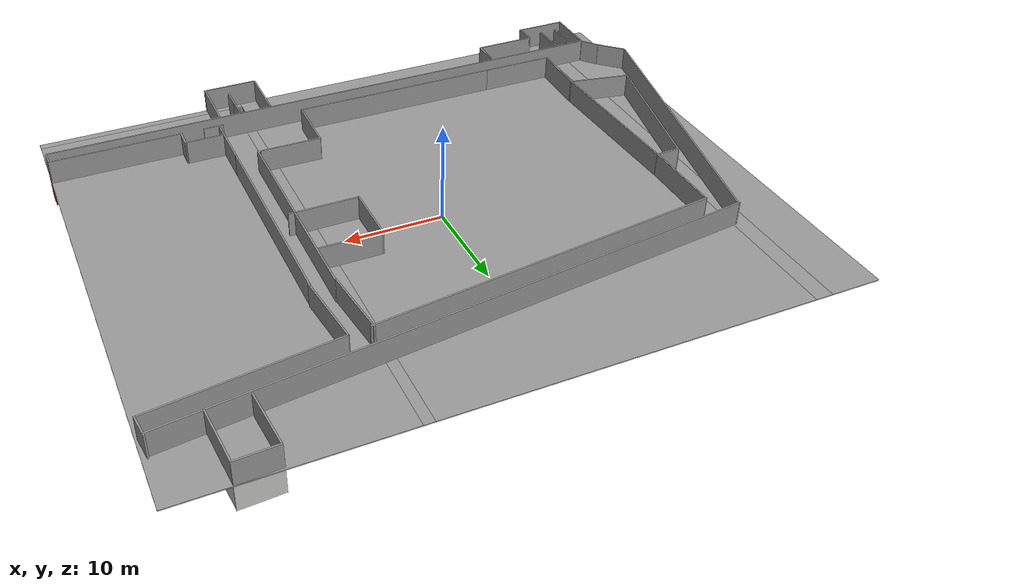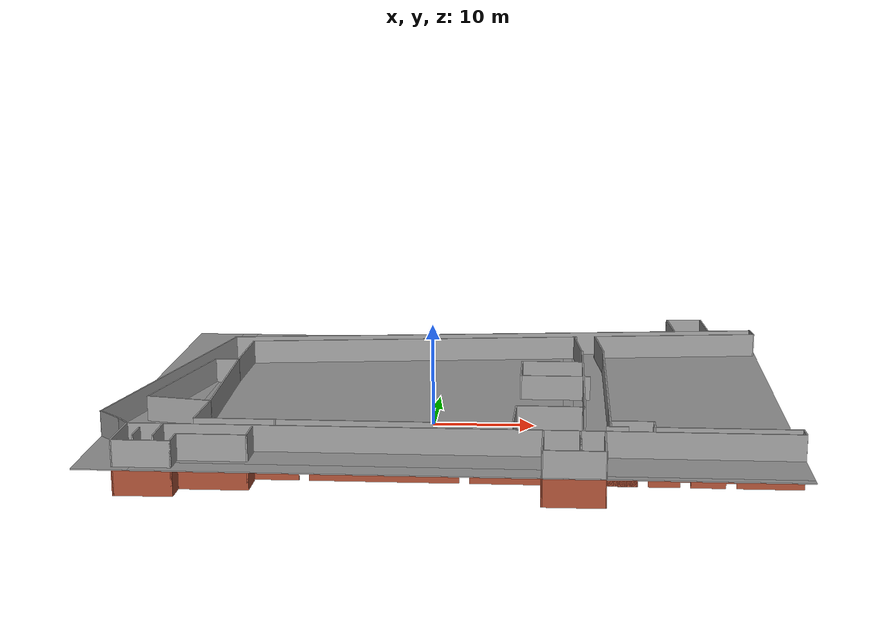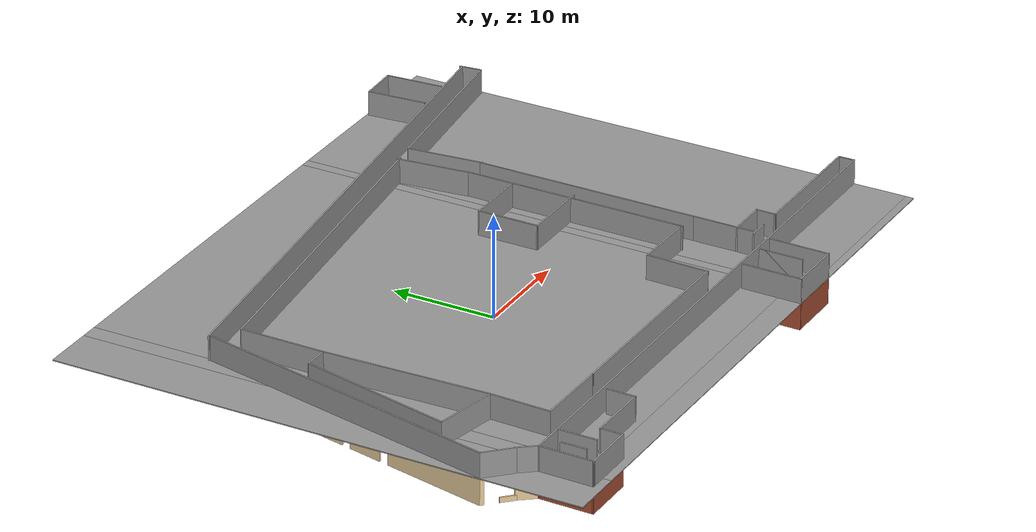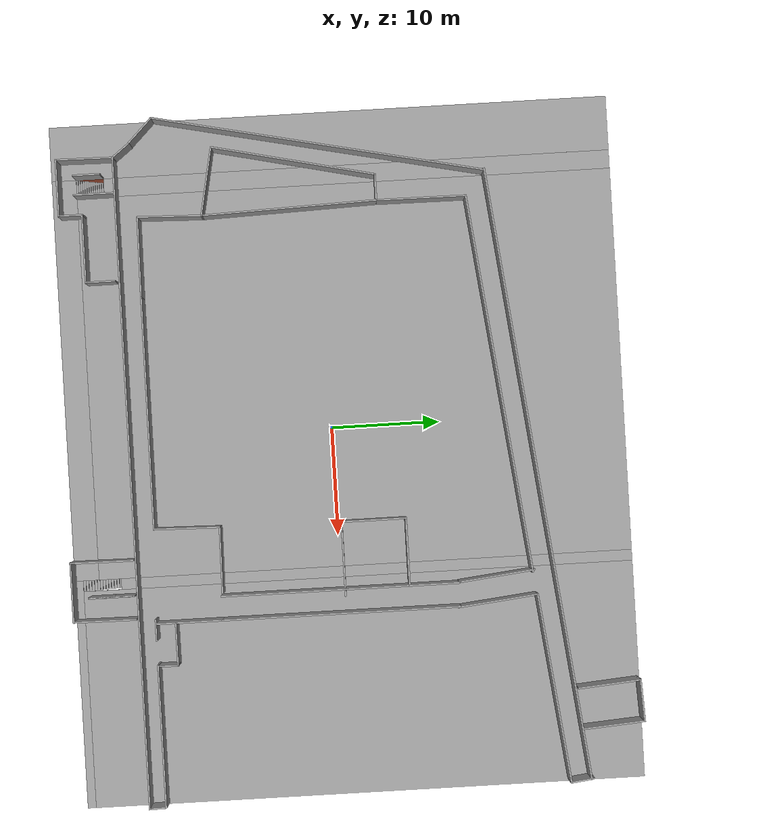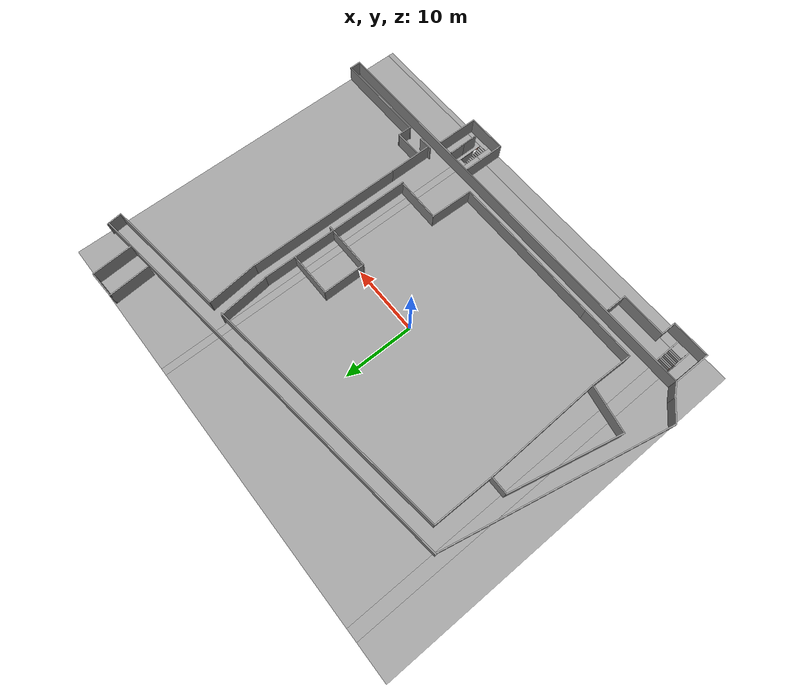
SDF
<?xml version='1.0'?>
<sdf version='1.6'>
  <model name='FokusFloor2-colour'>
    <pose frame=''>2.32223 1.2425 0 0 -0 0</pose>
    <link name='Floor_0'>
      <pose frame=''>1e-06 0 2.5 0 -0 0</pose>
      <visual name='Floor_0_Visual_0'>
        <pose frame=''>-28.8524 0 0.05 0 -0 0</pose>
        <geometry>
          <box>
            <size>4.9433 51.2587 0.1</size>
          </box>
        </geometry>
        <material>
          <script>
            <uri>file://media/materials/scripts/gazebo.material</uri>
            <name>Gazebo/Grey</name>
          </script>
          <ambient>1 1 1 1</ambient>
        </material>
        <meta>
          <layer>1</layer>
        </meta>
      </visual>
      <collision name='Floor_0_Collision_0'>
        <geometry>
          <box>
            <size>4.9433 51.2587 0.1</size>
          </box>
        </geometry>
        <pose frame=''>-28.8524 0 0.05 0 -0 0</pose>
      </collision>
      <visual name='Floor_0_Visual_1'>
        <pose frame=''>-7.97961 -24.5137 0.05 0 -0 0</pose>
        <geometry>
          <box>
            <size>36.8022 2.23126 0.1</size>
          </box>
        </geometry>
        <material>
          <script>
            <uri>file://media/materials/scripts/gazebo.material</uri>
            <name>Gazebo/Grey</name>
          </script>
          <ambient>1 1 1 1</ambient>
        </material>
        <meta>
          <layer>1</layer>
        </meta>
      </visual>
      <collision name='Floor_0_Collision_1'>
        <geometry>
          <box>
            <size>36.8022 2.23126 0.1</size>
          </box>
        </geometry>
        <pose frame=''>-7.97961 -24.5137 0.05 0 -0 0</pose>
      </collision>
      <visual name='Floor_0_Visual_2'>
        <pose frame=''>20.8727 -25.2512 0.05 0 -0 0</pose>
        <geometry>
          <box>
            <size>20.9025 0.756323 0.1</size>
          </box>
        </geometry>
        <material>
          <script>
            <uri>file://media/materials/scripts/gazebo.material</uri>
            <name>Gazebo/Grey</name>
          </script>
          <ambient>1 1 1 1</ambient>
        </material>
        <meta>
          <layer>1</layer>
        </meta>
      </visual>
      <collision name='Floor_0_Collision_2'>
        <geometry>
          <box>
            <size>20.9025 0.756323 0.1</size>
          </box>
        </geometry>
        <pose frame=''>20.8727 -25.2512 0.05 0 -0 0</pose>
      </collision>
      <visual name='Floor_0_Visual_3'>
        <pose frame=''>21.3727 0.378161 0.05 0 -0 0</pose>
        <geometry>
          <box>
            <size>19.9025 50.5024 0.1</size>
          </box>
        </geometry>
        <material>
          <script>
            <uri>file://media/materials/scripts/gazebo.material</uri>
            <name>Gazebo/Grey</name>
          </script>
          <ambient>1 1 1 1</ambient>
        </material>
        <meta>
          <layer>1</layer>
        </meta>
      </visual>
      <collision name='Floor_0_Collision_3'>
        <geometry>
          <box>
            <size>19.9025 50.5024 0.1</size>
          </box>
        </geometry>
        <pose frame=''>21.3727 0.378161 0.05 0 -0 0</pose>
      </collision>
      <visual name='Floor_0_Visual_4'>
        <pose frame=''>-7.1357 1.11563 0.05 0 -0 0</pose>
        <geometry>
          <box>
            <size>35.1144 49.0274 0.1</size>
          </box>
        </geometry>
        <material>
          <script>
            <uri>file://media/materials/scripts/gazebo.material</uri>
            <name>Gazebo/Grey</name>
          </script>
          <ambient>1 1 1 1</ambient>
        </material>
        <meta>
          <layer>1</layer>
        </meta>
      </visual>
      <collision name='Floor_0_Collision_4'>
        <geometry>
          <box>
            <size>35.1144 49.0274 0.1</size>
          </box>
        </geometry>
        <pose frame=''>-7.1357 1.11563 0.05 0 -0 0</pose>
      </collision>
      <visual name='Floor_0_Visual_5'>
        <pose frame=''>10.9215 2.12816 0.05 0 -0 0</pose>
        <geometry>
          <box>
            <size>1 47.0024 0.1</size>
          </box>
        </geometry>
        <material>
          <script>
            <uri>file://media/materials/scripts/gazebo.material</uri>
            <name>Gazebo/Grey</name>
          </script>
          <ambient>1 1 1 1</ambient>
        </material>
        <meta>
          <layer>1</layer>
        </meta>
      </visual>
      <collision name='Floor_0_Collision_5'>
        <geometry>
          <box>
            <size>1 47.0024 0.1</size>
          </box>
        </geometry>
        <pose frame=''>10.9215 2.12816 0.05 0 -0 0</pose>
      </collision>
      <visual name='Floor_0_Visual_6'>
        <pose frame=''>-25.5368 2.3722 0.05 0 -0 0</pose>
        <geometry>
          <box>
            <size>1.68782 46.5143 0.1</size>
          </box>
        </geometry>
        <material>
          <script>
            <uri>file://media/materials/scripts/gazebo.material</uri>
            <name>Gazebo/Grey</name>
          </script>
          <ambient>1 1 1 1</ambient>
        </material>
        <meta>
          <layer>1</layer>
        </meta>
      </visual>
      <collision name='Floor_0_Collision_6'>
        <geometry>
          <box>
            <size>1.68782 46.5143 0.1</size>
          </box>
        </geometry>
        <pose frame=''>-25.5368 2.3722 0.05 0 -0 0</pose>
      </collision>
    </link>
    <link name='Stairs_0'>
      <visual name='Stairs_0_Visual_0'>
        <pose frame=''>10.9215 -21.4897 0.083333 0 -0 0</pose>
        <geometry>
          <box>
            <size>1 0.233333 0.166667</size>
          </box>
        </geometry>
        <material>
          <script>
            <uri>file://media/materials/scripts/gazebo.material</uri>
            <name>Gazebo/Grey</name>
          </script>
          <ambient>1 1 1 1</ambient>
        </material>
        <meta>
          <layer>0</layer>
        </meta>
      </visual>
      <collision name='Stairs_0_Collision_0'>
        <geometry>
          <box>
            <size>1 0.233333 0.166667</size>
          </box>
        </geometry>
        <pose frame=''>10.9215 -21.4897 0.083333 0 -0 0</pose>
      </collision>
      <visual name='Stairs_0_Visual_1'>
        <pose frame=''>10.9215 -21.723 0.25 0 -0 0</pose>
        <geometry>
          <box>
            <size>1 0.233333 0.166667</size>
          </box>
        </geometry>
        <material>
          <script>
            <uri>file://media/materials/scripts/gazebo.material</uri>
            <name>Gazebo/Grey</name>
          </script>
          <ambient>1 1 1 1</ambient>
        </material>
        <meta>
          <layer>0</layer>
        </meta>
      </visual>
      <collision name='Stairs_0_Collision_1'>
        <geometry>
          <box>
            <size>1 0.233333 0.166667</size>
          </box>
        </geometry>
        <pose frame=''>10.9215 -21.723 0.25 0 -0 0</pose>
      </collision>
      <visual name='Stairs_0_Visual_2'>
        <pose frame=''>10.9215 -21.9564 0.416667 0 -0 0</pose>
        <geometry>
          <box>
            <size>1 0.233333 0.166667</size>
          </box>
        </geometry>
        <material>
          <script>
            <uri>file://media/materials/scripts/gazebo.material</uri>
            <name>Gazebo/Grey</name>
          </script>
          <ambient>1 1 1 1</ambient>
        </material>
        <meta>
          <layer>0</layer>
        </meta>
      </visual>
      <collision name='Stairs_0_Collision_2'>
        <geometry>
          <box>
            <size>1 0.233333 0.166667</size>
          </box>
        </geometry>
        <pose frame=''>10.9215 -21.9564 0.416667 0 -0 0</pose>
      </collision>
      <visual name='Stairs_0_Visual_3'>
        <pose frame=''>10.9215 -22.1897 0.583333 0 -0 0</pose>
        <geometry>
          <box>
            <size>1 0.233333 0.166667</size>
          </box>
        </geometry>
        <material>
          <script>
            <uri>file://media/materials/scripts/gazebo.material</uri>
            <name>Gazebo/Grey</name>
          </script>
          <ambient>1 1 1 1</ambient>
        </material>
        <meta>
          <layer>0</layer>
        </meta>
      </visual>
      <collision name='Stairs_0_Collision_3'>
        <geometry>
          <box>
            <size>1 0.233333 0.166667</size>
          </box>
        </geometry>
        <pose frame=''>10.9215 -22.1897 0.583333 0 -0 0</pose>
      </collision>
      <visual name='Stairs_0_Visual_4'>
        <pose frame=''>10.9215 -22.423 0.75 0 -0 0</pose>
        <geometry>
          <box>
            <size>1 0.233333 0.166667</size>
          </box>
        </geometry>
        <material>
          <script>
            <uri>file://media/materials/scripts/gazebo.material</uri>
            <name>Gazebo/Grey</name>
          </script>
          <ambient>1 1 1 1</ambient>
        </material>
        <meta>
          <layer>0</layer>
        </meta>
      </visual>
      <collision name='Stairs_0_Collision_4'>
        <geometry>
          <box>
            <size>1 0.233333 0.166667</size>
          </box>
        </geometry>
        <pose frame=''>10.9215 -22.423 0.75 0 -0 0</pose>
      </collision>
      <visual name='Stairs_0_Visual_5'>
        <pose frame=''>10.9215 -22.6564 0.916667 0 -0 0</pose>
        <geometry>
          <box>
            <size>1 0.233333 0.166667</size>
          </box>
        </geometry>
        <material>
          <script>
            <uri>file://media/materials/scripts/gazebo.material</uri>
            <name>Gazebo/Grey</name>
          </script>
          <ambient>1 1 1 1</ambient>
        </material>
        <meta>
          <layer>0</layer>
        </meta>
      </visual>
      <collision name='Stairs_0_Collision_5'>
        <geometry>
          <box>
            <size>1 0.233333 0.166667</size>
          </box>
        </geometry>
        <pose frame=''>10.9215 -22.6564 0.916667 0 -0 0</pose>
      </collision>
      <visual name='Stairs_0_Visual_6'>
        <pose frame=''>10.9215 -22.8897 1.08333 0 -0 0</pose>
        <geometry>
          <box>
            <size>1 0.233333 0.166667</size>
          </box>
        </geometry>
        <material>
          <script>
            <uri>file://media/materials/scripts/gazebo.material</uri>
            <name>Gazebo/Grey</name>
          </script>
          <ambient>1 1 1 1</ambient>
        </material>
        <meta>
          <layer>0</layer>
        </meta>
      </visual>
      <collision name='Stairs_0_Collision_6'>
        <geometry>
          <box>
            <size>1 0.233333 0.166667</size>
          </box>
        </geometry>
        <pose frame=''>10.9215 -22.8897 1.08333 0 -0 0</pose>
      </collision>
      <visual name='Stairs_0_Visual_7'>
        <pose frame=''>10.9215 -23.123 1.25 0 -0 0</pose>
        <geometry>
          <box>
            <size>1 0.233333 0.166667</size>
          </box>
        </geometry>
        <material>
          <script>
            <uri>file://media/materials/scripts/gazebo.material</uri>
            <name>Gazebo/Grey</name>
          </script>
          <ambient>1 1 1 1</ambient>
        </material>
        <meta>
          <layer>0</layer>
        </meta>
      </visual>
      <collision name='Stairs_0_Collision_7'>
        <geometry>
          <box>
            <size>1 0.233333 0.166667</size>
          </box>
        </geometry>
        <pose frame=''>10.9215 -23.123 1.25 0 -0 0</pose>
      </collision>
      <visual name='Stairs_0_Visual_8'>
        <pose frame=''>10.9215 -23.3564 1.41667 0 -0 0</pose>
        <geometry>
          <box>
            <size>1 0.233333 0.166667</size>
          </box>
        </geometry>
        <material>
          <script>
            <uri>file://media/materials/scripts/gazebo.material</uri>
            <name>Gazebo/Grey</name>
          </script>
          <ambient>1 1 1 1</ambient>
        </material>
        <meta>
          <layer>0</layer>
        </meta>
      </visual>
      <collision name='Stairs_0_Collision_8'>
        <geometry>
          <box>
            <size>1 0.233333 0.166667</size>
          </box>
        </geometry>
        <pose frame=''>10.9215 -23.3564 1.41667 0 -0 0</pose>
      </collision>
      <visual name='Stairs_0_Visual_9'>
        <pose frame=''>10.9215 -23.5897 1.58333 0 -0 0</pose>
        <geometry>
          <box>
            <size>1 0.233333 0.166667</size>
          </box>
        </geometry>
        <material>
          <script>
            <uri>file://media/materials/scripts/gazebo.material</uri>
            <name>Gazebo/Grey</name>
          </script>
          <ambient>1 1 1 1</ambient>
        </material>
        <meta>
          <layer>0</layer>
        </meta>
      </visual>
      <collision name='Stairs_0_Collision_9'>
        <geometry>
          <box>
            <size>1 0.233333 0.166667</size>
          </box>
        </geometry>
        <pose frame=''>10.9215 -23.5897 1.58333 0 -0 0</pose>
      </collision>
      <visual name='Stairs_0_Visual_10'>
        <pose frame=''>10.9215 -23.823 1.75 0 -0 0</pose>
        <geometry>
          <box>
            <size>1 0.233333 0.166667</size>
          </box>
        </geometry>
        <material>
          <script>
            <uri>file://media/materials/scripts/gazebo.material</uri>
            <name>Gazebo/Grey</name>
          </script>
          <ambient>1 1 1 1</ambient>
        </material>
        <meta>
          <layer>0</layer>
        </meta>
      </visual>
      <collision name='Stairs_0_Collision_10'>
        <geometry>
          <box>
            <size>1 0.233333 0.166667</size>
          </box>
        </geometry>
        <pose frame=''>10.9215 -23.823 1.75 0 -0 0</pose>
      </collision>
      <visual name='Stairs_0_Visual_11'>
        <pose frame=''>10.9215 -24.0564 1.91667 0 -0 0</pose>
        <geometry>
          <box>
            <size>1 0.233333 0.166667</size>
          </box>
        </geometry>
        <material>
          <script>
            <uri>file://media/materials/scripts/gazebo.material</uri>
            <name>Gazebo/Grey</name>
          </script>
          <ambient>1 1 1 1</ambient>
        </material>
        <meta>
          <layer>0</layer>
        </meta>
      </visual>
      <collision name='Stairs_0_Collision_11'>
        <geometry>
          <box>
            <size>1 0.233333 0.166667</size>
          </box>
        </geometry>
        <pose frame=''>10.9215 -24.0564 1.91667 0 -0 0</pose>
      </collision>
      <visual name='Stairs_0_Visual_12'>
        <pose frame=''>10.9215 -24.2897 2.08333 0 -0 0</pose>
        <geometry>
          <box>
            <size>1 0.233333 0.166667</size>
          </box>
        </geometry>
        <material>
          <script>
            <uri>file://media/materials/scripts/gazebo.material</uri>
            <name>Gazebo/Grey</name>
          </script>
          <ambient>1 1 1 1</ambient>
        </material>
        <meta>
          <layer>0</layer>
        </meta>
      </visual>
      <collision name='Stairs_0_Collision_12'>
        <geometry>
          <box>
            <size>1 0.233333 0.166667</size>
          </box>
        </geometry>
        <pose frame=''>10.9215 -24.2897 2.08333 0 -0 0</pose>
      </collision>
      <visual name='Stairs_0_Visual_13'>
        <pose frame=''>10.9215 -24.523 2.25 0 -0 0</pose>
        <geometry>
          <box>
            <size>1 0.233333 0.166667</size>
          </box>
        </geometry>
        <material>
          <script>
            <uri>file://media/materials/scripts/gazebo.material</uri>
            <name>Gazebo/Grey</name>
          </script>
          <ambient>1 1 1 1</ambient>
        </material>
        <meta>
          <layer>0</layer>
        </meta>
      </visual>
      <collision name='Stairs_0_Collision_13'>
        <geometry>
          <box>
            <size>1 0.233333 0.166667</size>
          </box>
        </geometry>
        <pose frame=''>10.9215 -24.523 2.25 0 -0 0</pose>
      </collision>
      <visual name='Stairs_0_Visual_14'>
        <pose frame=''>10.9215 -24.7564 2.41667 0 -0 0</pose>
        <geometry>
          <box>
            <size>1 0.233333 0.166667</size>
          </box>
        </geometry>
        <material>
          <script>
            <uri>file://media/materials/scripts/gazebo.material</uri>
            <name>Gazebo/Grey</name>
          </script>
          <ambient>1 1 1 1</ambient>
        </material>
        <meta>
          <layer>0</layer>
        </meta>
      </visual>
      <collision name='Stairs_0_Collision_14'>
        <geometry>
          <box>
            <size>1 0.233333 0.166667</size>
          </box>
        </geometry>
        <pose frame=''>10.9215 -24.7564 2.41667 0 -0 0</pose>
      </collision>
    </link>
    <link name='Stairs_1'>
      <visual name='Stairs_1_Visual_0'>
        <pose frame=''>-25.5368 -20.9687 0.083333 0 -0 0</pose>
        <geometry>
          <box>
            <size>1.68782 0.167542 0.166667</size>
          </box>
        </geometry>
        <material>
          <script>
            <uri>file://media/materials/scripts/gazebo.material</uri>
            <name>Gazebo/Grey</name>
          </script>
          <ambient>1 1 1 1</ambient>
        </material>
        <meta>
          <layer>0</layer>
        </meta>
      </visual>
      <collision name='Stairs_1_Collision_0'>
        <geometry>
          <box>
            <size>1.68782 0.167542 0.166667</size>
          </box>
        </geometry>
        <pose frame=''>-25.5368 -20.9687 0.083333 0 -0 0</pose>
      </collision>
      <visual name='Stairs_1_Visual_1'>
        <pose frame=''>-25.5368 -21.1363 0.25 0 -0 0</pose>
        <geometry>
          <box>
            <size>1.68782 0.167542 0.166667</size>
          </box>
        </geometry>
        <material>
          <script>
            <uri>file://media/materials/scripts/gazebo.material</uri>
            <name>Gazebo/Grey</name>
          </script>
          <ambient>1 1 1 1</ambient>
        </material>
        <meta>
          <layer>0</layer>
        </meta>
      </visual>
      <collision name='Stairs_1_Collision_1'>
        <geometry>
          <box>
            <size>1.68782 0.167542 0.166667</size>
          </box>
        </geometry>
        <pose frame=''>-25.5368 -21.1363 0.25 0 -0 0</pose>
      </collision>
      <visual name='Stairs_1_Visual_2'>
        <pose frame=''>-25.5368 -21.3038 0.416667 0 -0 0</pose>
        <geometry>
          <box>
            <size>1.68782 0.167542 0.166667</size>
          </box>
        </geometry>
        <material>
          <script>
            <uri>file://media/materials/scripts/gazebo.material</uri>
            <name>Gazebo/Grey</name>
          </script>
          <ambient>1 1 1 1</ambient>
        </material>
        <meta>
          <layer>0</layer>
        </meta>
      </visual>
      <collision name='Stairs_1_Collision_2'>
        <geometry>
          <box>
            <size>1.68782 0.167542 0.166667</size>
          </box>
        </geometry>
        <pose frame=''>-25.5368 -21.3038 0.416667 0 -0 0</pose>
      </collision>
      <visual name='Stairs_1_Visual_3'>
        <pose frame=''>-25.5368 -21.4714 0.583333 0 -0 0</pose>
        <geometry>
          <box>
            <size>1.68782 0.167542 0.166667</size>
          </box>
        </geometry>
        <material>
          <script>
            <uri>file://media/materials/scripts/gazebo.material</uri>
            <name>Gazebo/Grey</name>
          </script>
          <ambient>1 1 1 1</ambient>
        </material>
        <meta>
          <layer>0</layer>
        </meta>
      </visual>
      <collision name='Stairs_1_Collision_3'>
        <geometry>
          <box>
            <size>1.68782 0.167542 0.166667</size>
          </box>
        </geometry>
        <pose frame=''>-25.5368 -21.4714 0.583333 0 -0 0</pose>
      </collision>
      <visual name='Stairs_1_Visual_4'>
        <pose frame=''>-25.5368 -21.6389 0.75 0 -0 0</pose>
        <geometry>
          <box>
            <size>1.68782 0.167542 0.166667</size>
          </box>
        </geometry>
        <material>
          <script>
            <uri>file://media/materials/scripts/gazebo.material</uri>
            <name>Gazebo/Grey</name>
          </script>
          <ambient>1 1 1 1</ambient>
        </material>
        <meta>
          <layer>0</layer>
        </meta>
      </visual>
      <collision name='Stairs_1_Collision_4'>
        <geometry>
          <box>
            <size>1.68782 0.167542 0.166667</size>
          </box>
        </geometry>
        <pose frame=''>-25.5368 -21.6389 0.75 0 -0 0</pose>
      </collision>
      <visual name='Stairs_1_Visual_5'>
        <pose frame=''>-25.5368 -21.8064 0.916667 0 -0 0</pose>
        <geometry>
          <box>
            <size>1.68782 0.167542 0.166667</size>
          </box>
        </geometry>
        <material>
          <script>
            <uri>file://media/materials/scripts/gazebo.material</uri>
            <name>Gazebo/Grey</name>
          </script>
          <ambient>1 1 1 1</ambient>
        </material>
        <meta>
          <layer>0</layer>
        </meta>
      </visual>
      <collision name='Stairs_1_Collision_5'>
        <geometry>
          <box>
            <size>1.68782 0.167542 0.166667</size>
          </box>
        </geometry>
        <pose frame=''>-25.5368 -21.8064 0.916667 0 -0 0</pose>
      </collision>
      <visual name='Stairs_1_Visual_6'>
        <pose frame=''>-25.5368 -21.974 1.08333 0 -0 0</pose>
        <geometry>
          <box>
            <size>1.68782 0.167542 0.166667</size>
          </box>
        </geometry>
        <material>
          <script>
            <uri>file://media/materials/scripts/gazebo.material</uri>
            <name>Gazebo/Grey</name>
          </script>
          <ambient>1 1 1 1</ambient>
        </material>
        <meta>
          <layer>0</layer>
        </meta>
      </visual>
      <collision name='Stairs_1_Collision_6'>
        <geometry>
          <box>
            <size>1.68782 0.167542 0.166667</size>
          </box>
        </geometry>
        <pose frame=''>-25.5368 -21.974 1.08333 0 -0 0</pose>
      </collision>
      <visual name='Stairs_1_Visual_7'>
        <pose frame=''>-25.5368 -22.1415 1.25 0 -0 0</pose>
        <geometry>
          <box>
            <size>1.68782 0.167542 0.166667</size>
          </box>
        </geometry>
        <material>
          <script>
            <uri>file://media/materials/scripts/gazebo.material</uri>
            <name>Gazebo/Grey</name>
          </script>
          <ambient>1 1 1 1</ambient>
        </material>
        <meta>
          <layer>0</layer>
        </meta>
      </visual>
      <collision name='Stairs_1_Collision_7'>
        <geometry>
          <box>
            <size>1.68782 0.167542 0.166667</size>
          </box>
        </geometry>
        <pose frame=''>-25.5368 -22.1415 1.25 0 -0 0</pose>
      </collision>
      <visual name='Stairs_1_Visual_8'>
        <pose frame=''>-25.5368 -22.3091 1.41667 0 -0 0</pose>
        <geometry>
          <box>
            <size>1.68782 0.167542 0.166667</size>
          </box>
        </geometry>
        <material>
          <script>
            <uri>file://media/materials/scripts/gazebo.material</uri>
            <name>Gazebo/Grey</name>
          </script>
          <ambient>1 1 1 1</ambient>
        </material>
        <meta>
          <layer>0</layer>
        </meta>
      </visual>
      <collision name='Stairs_1_Collision_8'>
        <geometry>
          <box>
            <size>1.68782 0.167542 0.166667</size>
          </box>
        </geometry>
        <pose frame=''>-25.5368 -22.3091 1.41667 0 -0 0</pose>
      </collision>
      <visual name='Stairs_1_Visual_9'>
        <pose frame=''>-25.5368 -22.4766 1.58333 0 -0 0</pose>
        <geometry>
          <box>
            <size>1.68782 0.167542 0.166667</size>
          </box>
        </geometry>
        <material>
          <script>
            <uri>file://media/materials/scripts/gazebo.material</uri>
            <name>Gazebo/Grey</name>
          </script>
          <ambient>1 1 1 1</ambient>
        </material>
        <meta>
          <layer>0</layer>
        </meta>
      </visual>
      <collision name='Stairs_1_Collision_9'>
        <geometry>
          <box>
            <size>1.68782 0.167542 0.166667</size>
          </box>
        </geometry>
        <pose frame=''>-25.5368 -22.4766 1.58333 0 -0 0</pose>
      </collision>
      <visual name='Stairs_1_Visual_10'>
        <pose frame=''>-25.5368 -22.6442 1.75 0 -0 0</pose>
        <geometry>
          <box>
            <size>1.68782 0.167542 0.166667</size>
          </box>
        </geometry>
        <material>
          <script>
            <uri>file://media/materials/scripts/gazebo.material</uri>
            <name>Gazebo/Grey</name>
          </script>
          <ambient>1 1 1 1</ambient>
        </material>
        <meta>
          <layer>0</layer>
        </meta>
      </visual>
      <collision name='Stairs_1_Collision_10'>
        <geometry>
          <box>
            <size>1.68782 0.167542 0.166667</size>
          </box>
        </geometry>
        <pose frame=''>-25.5368 -22.6442 1.75 0 -0 0</pose>
      </collision>
      <visual name='Stairs_1_Visual_11'>
        <pose frame=''>-25.5368 -22.8117 1.91667 0 -0 0</pose>
        <geometry>
          <box>
            <size>1.68782 0.167542 0.166667</size>
          </box>
        </geometry>
        <material>
          <script>
            <uri>file://media/materials/scripts/gazebo.material</uri>
            <name>Gazebo/Grey</name>
          </script>
          <ambient>1 1 1 1</ambient>
        </material>
        <meta>
          <layer>0</layer>
        </meta>
      </visual>
      <collision name='Stairs_1_Collision_11'>
        <geometry>
          <box>
            <size>1.68782 0.167542 0.166667</size>
          </box>
        </geometry>
        <pose frame=''>-25.5368 -22.8117 1.91667 0 -0 0</pose>
      </collision>
      <visual name='Stairs_1_Visual_12'>
        <pose frame=''>-25.5368 -22.9792 2.08333 0 -0 0</pose>
        <geometry>
          <box>
            <size>1.68782 0.167542 0.166667</size>
          </box>
        </geometry>
        <material>
          <script>
            <uri>file://media/materials/scripts/gazebo.material</uri>
            <name>Gazebo/Grey</name>
          </script>
          <ambient>1 1 1 1</ambient>
        </material>
        <meta>
          <layer>0</layer>
        </meta>
      </visual>
      <collision name='Stairs_1_Collision_12'>
        <geometry>
          <box>
            <size>1.68782 0.167542 0.166667</size>
          </box>
        </geometry>
        <pose frame=''>-25.5368 -22.9792 2.08333 0 -0 0</pose>
      </collision>
      <visual name='Stairs_1_Visual_13'>
        <pose frame=''>-25.5368 -23.1468 2.25 0 -0 0</pose>
        <geometry>
          <box>
            <size>1.68782 0.167542 0.166667</size>
          </box>
        </geometry>
        <material>
          <script>
            <uri>file://media/materials/scripts/gazebo.material</uri>
            <name>Gazebo/Grey</name>
          </script>
          <ambient>1 1 1 1</ambient>
        </material>
        <meta>
          <layer>0</layer>
        </meta>
      </visual>
      <collision name='Stairs_1_Collision_13'>
        <geometry>
          <box>
            <size>1.68782 0.167542 0.166667</size>
          </box>
        </geometry>
        <pose frame=''>-25.5368 -23.1468 2.25 0 -0 0</pose>
      </collision>
      <visual name='Stairs_1_Visual_14'>
        <pose frame=''>-25.5368 -23.3143 2.41667 0 -0 0</pose>
        <geometry>
          <box>
            <size>1.68782 0.167542 0.166667</size>
          </box>
        </geometry>
        <material>
          <script>
            <uri>file://media/materials/scripts/gazebo.material</uri>
            <name>Gazebo/Grey</name>
          </script>
          <ambient>1 1 1 1</ambient>
        </material>
        <meta>
          <layer>0</layer>
        </meta>
      </visual>
      <collision name='Stairs_1_Collision_14'>
        <geometry>
          <box>
            <size>1.68782 0.167542 0.166667</size>
          </box>
        </geometry>
        <pose frame=''>-25.5368 -23.3143 2.41667 0 -0 0</pose>
      </collision>
    </link>
    <link name='Wall_0'>
      <pose frame=''>1.68206 -19.6458 0 0 -0 0</pose>
      <visual name='Wall_0_Visual_0'>
        <pose frame=''>-27.675 0 1.25 0 -0 0</pose>
        <geometry>
          <box>
            <size>3.89998 0.15 2.5</size>
          </box>
        </geometry>
        <material>
          <script>
            <uri>file://media/materials/scripts/gazebo.material</uri>
            <name>Gazebo/Bricks</name>
          </script>
          <ambient>1 1 1 1</ambient>
        </material>
        <meta>
          <layer>0</layer>
        </meta>
      </visual>
      <collision name='Wall_0_Collision_0'>
        <geometry>
          <box>
            <size>3.89998 0.15 2.5</size>
          </box>
        </geometry>
        <pose frame=''>-27.675 0 1.25 0 -0 0</pose>
      </collision>
      <visual name='Wall_0_Visual_1'>
        <pose frame=''>-19.6116 0 1.25 0 -0 0</pose>
        <geometry>
          <box>
            <size>10.4269 0.15 2.5</size>
          </box>
        </geometry>
        <material>
          <script>
            <uri>file://media/materials/scripts/gazebo.material</uri>
            <name>Gazebo/Bricks</name>
          </script>
          <ambient>1 1 1 1</ambient>
        </material>
        <meta>
          <layer>0</layer>
        </meta>
      </visual>
      <collision name='Wall_0_Collision_1'>
        <geometry>
          <box>
            <size>10.4269 0.15 2.5</size>
          </box>
        </geometry>
        <pose frame=''>-19.6116 0 1.25 0 -0 0</pose>
      </collision>
      <visual name='Wall_0_Visual_2'>
        <pose frame=''>-6.88407 0 1.25 0 -0 0</pose>
        <geometry>
          <box>
            <size>13.2282 0.15 2.5</size>
          </box>
        </geometry>
        <material>
          <script>
            <uri>file://media/materials/scripts/gazebo.material</uri>
            <name>Gazebo/Bricks</name>
          </script>
          <ambient>1 1 1 1</ambient>
        </material>
        <meta>
          <layer>0</layer>
        </meta>
      </visual>
      <collision name='Wall_0_Collision_2'>
        <geometry>
          <box>
            <size>13.2282 0.15 2.5</size>
          </box>
        </geometry>
        <pose frame=''>-6.88407 0 1.25 0 -0 0</pose>
      </collision>
      <visual name='Wall_0_Visual_3'>
        <pose frame=''>5.50623 0 1.25 0 -0 0</pose>
        <geometry>
          <box>
            <size>9.75238 0.15 2.5</size>
          </box>
        </geometry>
        <material>
          <script>
            <uri>file://media/materials/scripts/gazebo.material</uri>
            <name>Gazebo/Bricks</name>
          </script>
          <ambient>1 1 1 1</ambient>
        </material>
        <meta>
          <layer>0</layer>
        </meta>
      </visual>
      <collision name='Wall_0_Collision_3'>
        <geometry>
          <box>
            <size>9.75238 0.15 2.5</size>
          </box>
        </geometry>
        <pose frame=''>5.50623 0 1.25 0 -0 0</pose>
      </collision>
      <visual name='Wall_0_Visual_4'>
        <pose frame=''>13.2652 0 1.25 0 -0 0</pose>
        <geometry>
          <box>
            <size>3.96562 0.15 2.5</size>
          </box>
        </geometry>
        <material>
          <script>
            <uri>file://media/materials/scripts/gazebo.material</uri>
            <name>Gazebo/Bricks</name>
          </script>
          <ambient>1 1 1 1</ambient>
        </material>
        <meta>
          <layer>0</layer>
        </meta>
      </visual>
      <collision name='Wall_0_Collision_4'>
        <geometry>
          <box>
            <size>3.96562 0.15 2.5</size>
          </box>
        </geometry>
        <pose frame=''>13.2652 0 1.25 0 -0 0</pose>
      </collision>
      <visual name='Wall_0_Visual_5'>
        <pose frame=''>13.7123 0 1.25 0 -0 0</pose>
        <geometry>
          <box>
            <size>3.0714 0.15 2.5</size>
          </box>
        </geometry>
        <material>
          <script>
            <uri>file://media/materials/scripts/gazebo.material</uri>
            <name>Gazebo/Bricks</name>
          </script>
          <ambient>1 1 1 1</ambient>
        </material>
        <meta>
          <layer>0</layer>
        </meta>
      </visual>
      <collision name='Wall_0_Collision_5'>
        <geometry>
          <box>
            <size>3.0714 0.15 2.5</size>
          </box>
        </geometry>
        <pose frame=''>13.7123 0 1.25 0 -0 0</pose>
      </collision>
      <visual name='Wall_0_Visual_6'>
        <pose frame=''>17.5391 0 1.25 0 -0 0</pose>
        <geometry>
          <box>
            <size>2.78209 0.15 2.5</size>
          </box>
        </geometry>
        <material>
          <script>
            <uri>file://media/materials/scripts/gazebo.material</uri>
            <name>Gazebo/Bricks</name>
          </script>
          <ambient>1 1 1 1</ambient>
        </material>
        <meta>
          <layer>0</layer>
        </meta>
      </visual>
      <collision name='Wall_0_Collision_6'>
        <geometry>
          <box>
            <size>2.78209 0.15 2.5</size>
          </box>
        </geometry>
        <pose frame=''>17.5391 0 1.25 0 -0 0</pose>
      </collision>
      <visual name='Wall_0_Visual_7'>
        <pose frame=''>21.3527 0 1.25 0 -0 0</pose>
        <geometry>
          <box>
            <size>3.0451 0.15 2.5</size>
          </box>
        </geometry>
        <material>
          <script>
            <uri>file://media/materials/scripts/gazebo.material</uri>
            <name>Gazebo/Bricks</name>
          </script>
          <ambient>1 1 1 1</ambient>
        </material>
        <meta>
          <layer>0</layer>
        </meta>
      </visual>
      <collision name='Wall_0_Collision_7'>
        <geometry>
          <box>
            <size>3.0451 0.15 2.5</size>
          </box>
        </geometry>
        <pose frame=''>21.3527 0 1.25 0 -0 0</pose>
      </collision>
      <visual name='Wall_0_Visual_8'>
        <pose frame=''>26.7001 0 1.25 0 -0 0</pose>
        <geometry>
          <box>
            <size>5.84977 0.15 2.5</size>
          </box>
        </geometry>
        <material>
          <script>
            <uri>file://media/materials/scripts/gazebo.material</uri>
            <name>Gazebo/Bricks</name>
          </script>
          <ambient>1 1 1 1</ambient>
        </material>
        <meta>
          <layer>0</layer>
        </meta>
      </visual>
      <collision name='Wall_0_Collision_8'>
        <geometry>
          <box>
            <size>5.84977 0.15 2.5</size>
          </box>
        </geometry>
        <pose frame=''>26.7001 0 1.25 0 -0 0</pose>
      </collision>
      <visual name='Wall_0_Visual_9'>
        <pose frame=''>-25.275 0 2.25 0 -0 0</pose>
        <geometry>
          <box>
            <size>0.9 0.15 0.5</size>
          </box>
        </geometry>
        <material>
          <script>
            <uri>file://media/materials/scripts/gazebo.material</uri>
            <name>Gazebo/Bricks</name>
          </script>
          <ambient>1 1 1 1</ambient>
        </material>
        <meta>
          <layer>0</layer>
        </meta>
      </visual>
      <collision name='Wall_0_Collision_9'>
        <geometry>
          <box>
            <size>0.9 0.15 0.5</size>
          </box>
        </geometry>
        <pose frame=''>-25.275 0 2.25 0 -0 0</pose>
      </collision>
      <visual name='Wall_0_Visual_10'>
        <pose frame=''>-13.9482 0 2.25 0 -0 0</pose>
        <geometry>
          <box>
            <size>0.9 0.15 0.5</size>
          </box>
        </geometry>
        <material>
          <script>
            <uri>file://media/materials/scripts/gazebo.material</uri>
            <name>Gazebo/Bricks</name>
          </script>
          <ambient>1 1 1 1</ambient>
        </material>
        <meta>
          <layer>0</layer>
        </meta>
      </visual>
      <collision name='Wall_0_Collision_10'>
        <geometry>
          <box>
            <size>0.9 0.15 0.5</size>
          </box>
        </geometry>
        <pose frame=''>-13.9482 0 2.25 0 -0 0</pose>
      </collision>
      <visual name='Wall_0_Visual_11'>
        <pose frame=''>0.180036 0 2.25 0 -0 0</pose>
        <geometry>
          <box>
            <size>0.9 0.15 0.5</size>
          </box>
        </geometry>
        <material>
          <script>
            <uri>file://media/materials/scripts/gazebo.material</uri>
            <name>Gazebo/Bricks</name>
          </script>
          <ambient>1 1 1 1</ambient>
        </material>
        <meta>
          <layer>0</layer>
        </meta>
      </visual>
      <collision name='Wall_0_Collision_11'>
        <geometry>
          <box>
            <size>0.9 0.15 0.5</size>
          </box>
        </geometry>
        <pose frame=''>0.180036 0 2.25 0 -0 0</pose>
      </collision>
      <visual name='Wall_0_Visual_12'>
        <pose frame=''>10.8295 0 2.25 0 -0 0</pose>
        <geometry>
          <box>
            <size>0.894221 0.15 0.5</size>
          </box>
        </geometry>
        <material>
          <script>
            <uri>file://media/materials/scripts/gazebo.material</uri>
            <name>Gazebo/Bricks</name>
          </script>
          <ambient>1 1 1 1</ambient>
        </material>
        <meta>
          <layer>0</layer>
        </meta>
      </visual>
      <collision name='Wall_0_Collision_12'>
        <geometry>
          <box>
            <size>0.894221 0.15 0.5</size>
          </box>
        </geometry>
        <pose frame=''>10.8295 0 2.25 0 -0 0</pose>
      </collision>
      <visual name='Wall_0_Visual_13'>
        <pose frame=''>15.698 0 2.25 0 -0 0</pose>
        <geometry>
          <box>
            <size>0.9 0.15 0.5</size>
          </box>
        </geometry>
        <material>
          <script>
            <uri>file://media/materials/scripts/gazebo.material</uri>
            <name>Gazebo/Bricks</name>
          </script>
          <ambient>1 1 1 1</ambient>
        </material>
        <meta>
          <layer>0</layer>
        </meta>
      </visual>
      <collision name='Wall_0_Collision_13'>
        <geometry>
          <box>
            <size>0.9 0.15 0.5</size>
          </box>
        </geometry>
        <pose frame=''>15.698 0 2.25 0 -0 0</pose>
      </collision>
      <visual name='Wall_0_Visual_14'>
        <pose frame=''>15.698 0 2.25 0 -0 0</pose>
        <geometry>
          <box>
            <size>0.9 0.15 0.5</size>
          </box>
        </geometry>
        <material>
          <script>
            <uri>file://media/materials/scripts/gazebo.material</uri>
            <name>Gazebo/Bricks</name>
          </script>
          <ambient>1 1 1 1</ambient>
        </material>
        <meta>
          <layer>0</layer>
        </meta>
      </visual>
      <collision name='Wall_0_Collision_14'>
        <geometry>
          <box>
            <size>0.9 0.15 0.5</size>
          </box>
        </geometry>
        <pose frame=''>15.698 0 2.25 0 -0 0</pose>
      </collision>
      <visual name='Wall_0_Visual_15'>
        <pose frame=''>19.3801 0 2.25 0 -0 0</pose>
        <geometry>
          <box>
            <size>0.9 0.15 0.5</size>
          </box>
        </geometry>
        <material>
          <script>
            <uri>file://media/materials/scripts/gazebo.material</uri>
            <name>Gazebo/Bricks</name>
          </script>
          <ambient>1 1 1 1</ambient>
        </material>
        <meta>
          <layer>0</layer>
        </meta>
      </visual>
      <collision name='Wall_0_Collision_15'>
        <geometry>
          <box>
            <size>0.9 0.15 0.5</size>
          </box>
        </geometry>
        <pose frame=''>19.3801 0 2.25 0 -0 0</pose>
      </collision>
      <visual name='Wall_0_Visual_16'>
        <pose frame=''>23.3252 0 2.25 0 -0 0</pose>
        <geometry>
          <box>
            <size>0.9 0.15 0.5</size>
          </box>
        </geometry>
        <material>
          <script>
            <uri>file://media/materials/scripts/gazebo.material</uri>
            <name>Gazebo/Bricks</name>
          </script>
          <ambient>1 1 1 1</ambient>
        </material>
        <meta>
          <layer>0</layer>
        </meta>
      </visual>
      <collision name='Wall_0_Collision_16'>
        <geometry>
          <box>
            <size>0.9 0.15 0.5</size>
          </box>
        </geometry>
        <pose frame=''>23.3252 0 2.25 0 -0 0</pose>
      </collision>
    </link>
    <link name='Wall_1'>
      <collision name='Wall_1_Collision'>
        <geometry>
          <box>
            <size>1.57844 0.15 2.5</size>
          </box>
        </geometry>
        <pose frame=''>0 0 1.25 0 -0 0</pose>
      </collision>
      <visual name='Wall_1_Visual'>
        <pose frame=''>0 0 1.25 0 -0 0</pose>
        <geometry>
          <box>
            <size>1.57844 0.15 2.5</size>
          </box>
        </geometry>
        <material>
          <script>
            <uri>file://media/materials/scripts/gazebo.material</uri>
            <name>Gazebo/Bricks</name>
          </script>
          <ambient>1 1 1 1</ambient>
        </material>
        <meta>
          <layer>0</layer>
        </meta>
      </visual>
      <pose frame=''>31.2278 -18.9169 0 0 -0 1.59774</pose>
    </link>
    <link name='Wall_10'>
      <pose frame=''>-5.39207 14.1564 0 0 -0 -3.02197</pose>
      <visual name='Wall_10_Visual_0'>
        <pose frame=''>-13.8748 0 1.25 0 -0 0</pose>
        <geometry>
          <box>
            <size>7.02297 0.15 2.5</size>
          </box>
        </geometry>
        <material>
          <script>
            <uri>file://media/materials/scripts/gazebo.material</uri>
            <name>Gazebo/CeilingTiled</name>
          </script>
          <ambient>1 1 1 1</ambient>
        </material>
        <meta>
          <layer>0</layer>
        </meta>
      </visual>
      <collision name='Wall_10_Collision_0'>
        <geometry>
          <box>
            <size>7.02297 0.15 2.5</size>
          </box>
        </geometry>
        <pose frame=''>-13.8748 0 1.25 0 -0 0</pose>
      </collision>
      <visual name='Wall_10_Visual_1'>
        <pose frame=''>-7.70986 0 1.25 0 -0 0</pose>
        <geometry>
          <box>
            <size>3.50692 0.15 2.5</size>
          </box>
        </geometry>
        <material>
          <script>
            <uri>file://media/materials/scripts/gazebo.material</uri>
            <name>Gazebo/CeilingTiled</name>
          </script>
          <ambient>1 1 1 1</ambient>
        </material>
        <meta>
          <layer>0</layer>
        </meta>
      </visual>
      <collision name='Wall_10_Collision_1'>
        <geometry>
          <box>
            <size>3.50692 0.15 2.5</size>
          </box>
        </geometry>
        <pose frame=''>-7.70986 0 1.25 0 -0 0</pose>
      </collision>
      <visual name='Wall_10_Visual_2'>
        <pose frame=''>0.711653 0 1.25 0 -0 0</pose>
        <geometry>
          <box>
            <size>11.5361 0.15 2.5</size>
          </box>
        </geometry>
        <material>
          <script>
            <uri>file://media/materials/scripts/gazebo.material</uri>
            <name>Gazebo/CeilingTiled</name>
          </script>
          <ambient>1 1 1 1</ambient>
        </material>
        <meta>
          <layer>0</layer>
        </meta>
      </visual>
      <collision name='Wall_10_Collision_2'>
        <geometry>
          <box>
            <size>11.5361 0.15 2.5</size>
          </box>
        </geometry>
        <pose frame=''>0.711653 0 1.25 0 -0 0</pose>
      </collision>
      <visual name='Wall_10_Visual_3'>
        <pose frame=''>12.383 0 1.25 0 -0 0</pose>
        <geometry>
          <box>
            <size>10.0066 0.15 2.5</size>
          </box>
        </geometry>
        <material>
          <script>
            <uri>file://media/materials/scripts/gazebo.material</uri>
            <name>Gazebo/CeilingTiled</name>
          </script>
          <ambient>1 1 1 1</ambient>
        </material>
        <meta>
          <layer>0</layer>
        </meta>
      </visual>
      <collision name='Wall_10_Collision_3'>
        <geometry>
          <box>
            <size>10.0066 0.15 2.5</size>
          </box>
        </geometry>
        <pose frame=''>12.383 0 1.25 0 -0 0</pose>
      </collision>
      <visual name='Wall_10_Visual_4'>
        <pose frame=''>-9.91332 0 2.25 0 -0 0</pose>
        <geometry>
          <box>
            <size>0.9 0.15 0.5</size>
          </box>
        </geometry>
        <material>
          <script>
            <uri>file://media/materials/scripts/gazebo.material</uri>
            <name>Gazebo/CeilingTiled</name>
          </script>
          <ambient>1 1 1 1</ambient>
        </material>
        <meta>
          <layer>0</layer>
        </meta>
      </visual>
      <collision name='Wall_10_Collision_4'>
        <geometry>
          <box>
            <size>0.9 0.15 0.5</size>
          </box>
        </geometry>
        <pose frame=''>-9.91332 0 2.25 0 -0 0</pose>
      </collision>
      <visual name='Wall_10_Visual_5'>
        <pose frame=''>-5.5064 0 2.25 0 -0 0</pose>
        <geometry>
          <box>
            <size>0.9 0.15 0.5</size>
          </box>
        </geometry>
        <material>
          <script>
            <uri>file://media/materials/scripts/gazebo.material</uri>
            <name>Gazebo/CeilingTiled</name>
          </script>
          <ambient>1 1 1 1</ambient>
        </material>
        <meta>
          <layer>0</layer>
        </meta>
      </visual>
      <collision name='Wall_10_Collision_5'>
        <geometry>
          <box>
            <size>0.9 0.15 0.5</size>
          </box>
        </geometry>
        <pose frame=''>-5.5064 0 2.25 0 -0 0</pose>
      </collision>
      <visual name='Wall_10_Visual_6'>
        <pose frame=''>6.92971 0 2.25 0 -0 0</pose>
        <geometry>
          <box>
            <size>0.9 0.15 0.5</size>
          </box>
        </geometry>
        <material>
          <script>
            <uri>file://media/materials/scripts/gazebo.material</uri>
            <name>Gazebo/CeilingTiled</name>
          </script>
          <ambient>1 1 1 1</ambient>
        </material>
        <meta>
          <layer>0</layer>
        </meta>
      </visual>
      <collision name='Wall_10_Collision_6'>
        <geometry>
          <box>
            <size>0.9 0.15 0.5</size>
          </box>
        </geometry>
        <pose frame=''>6.92971 0 2.25 0 -0 0</pose>
      </collision>
    </link>
    <link name='Wall_100'>
      <collision name='Wall_100_Collision'>
        <geometry>
          <box>
            <size>2.06017 0.15 2.5</size>
          </box>
        </geometry>
        <pose frame=''>0 0 1.25 0 -0 0</pose>
      </collision>
      <visual name='Wall_100_Visual'>
        <pose frame=''>0 0 1.25 0 -0 0</pose>
        <geometry>
          <box>
            <size>2.06017 0.15 2.5</size>
          </box>
        </geometry>
        <material>
          <script>
            <uri>file://media/materials/scripts/gazebo.material</uri>
            <name>Gazebo/Grey</name>
          </script>
          <ambient>1 1 1 1</ambient>
        </material>
        <meta>
          <layer>1</layer>
        </meta>
      </visual>
      <pose frame=''>-28.4394 -18.8771 2.5 0 -0 -0.909626</pose>
    </link>
    <link name='Wall_101'>
      <collision name='Wall_101_Collision'>
        <geometry>
          <box>
            <size>8.22358 0.15 2.5</size>
          </box>
        </geometry>
        <pose frame=''>0 0 1.25 0 -0 0</pose>
      </collision>
      <visual name='Wall_101_Visual'>
        <pose frame=''>0 0 1.25 0 -0 0</pose>
        <geometry>
          <box>
            <size>8.22358 0.15 2.5</size>
          </box>
        </geometry>
        <material>
          <script>
            <uri>file://media/materials/scripts/gazebo.material</uri>
            <name>Gazebo/Grey</name>
          </script>
          <ambient>1 1 1 1</ambient>
        </material>
        <meta>
          <layer>1</layer>
        </meta>
      </visual>
      <pose frame=''>-22.6059 8.05384 2.5 0 -0 -1.57731</pose>
    </link>
    <link name='Wall_102'>
      <collision name='Wall_102_Collision'>
        <geometry>
          <box>
            <size>2.5 0.15 2.5</size>
          </box>
        </geometry>
        <pose frame=''>0 0 1.25 0 -0 0</pose>
      </collision>
      <visual name='Wall_102_Visual'>
        <pose frame=''>0 0 1.25 0 -0 0</pose>
        <geometry>
          <box>
            <size>2.5 0.15 2.5</size>
          </box>
        </geometry>
        <material>
          <script>
            <uri>file://media/materials/scripts/gazebo.material</uri>
            <name>Gazebo/Grey</name>
          </script>
          <ambient>1 1 1 1</ambient>
        </material>
        <meta>
          <layer>1</layer>
        </meta>
      </visual>
      <pose frame=''>-23.8072 3.99083 2.5 0 -0 3.14159</pose>
    </link>
    <link name='Wall_103'>
      <collision name='Wall_103_Collision'>
        <geometry>
          <box>
            <size>15.1732 0.15 2.5</size>
          </box>
        </geometry>
        <pose frame=''>0 0 1.25 0 -0 0</pose>
      </collision>
      <visual name='Wall_103_Visual'>
        <pose frame=''>0 0 1.25 0 -0 0</pose>
        <geometry>
          <box>
            <size>15.1732 0.15 2.5</size>
          </box>
        </geometry>
        <material>
          <script>
            <uri>file://media/materials/scripts/gazebo.material</uri>
            <name>Gazebo/Grey</name>
          </script>
          <ambient>1 1 1 1</ambient>
        </material>
        <meta>
          <layer>1</layer>
        </meta>
      </visual>
      <pose frame=''>-26.6296 -3.33792 2.5 0 -0 -1.79189</pose>
    </link>
    <link name='Wall_104'>
      <collision name='Wall_104_Collision'>
        <geometry>
          <box>
            <size>6.39727 0.15 2.5</size>
          </box>
        </geometry>
        <pose frame=''>0 0 1.25 0 -0 0</pose>
      </collision>
      <visual name='Wall_104_Visual'>
        <pose frame=''>0 0 1.25 0 -0 0</pose>
        <geometry>
          <box>
            <size>6.39727 0.15 2.5</size>
          </box>
        </geometry>
        <material>
          <script>
            <uri>file://media/materials/scripts/gazebo.material</uri>
            <name>Gazebo/Grey</name>
          </script>
          <ambient>1 1 1 1</ambient>
        </material>
        <meta>
          <layer>1</layer>
        </meta>
      </visual>
      <pose frame=''>-25.2124 -11.2983 2.5 0 -0 -0.195012</pose>
    </link>
    <link name='Wall_105'>
      <collision name='Wall_105_Collision'>
        <geometry>
          <box>
            <size>5.95032 0.15 2.5</size>
          </box>
        </geometry>
        <pose frame=''>0 0 1.25 0 -0 0</pose>
      </collision>
      <visual name='Wall_105_Visual'>
        <pose frame=''>0 0 1.25 0 -0 0</pose>
        <geometry>
          <box>
            <size>5.95032 0.15 2.5</size>
          </box>
        </geometry>
        <material>
          <script>
            <uri>file://media/materials/scripts/gazebo.material</uri>
            <name>Gazebo/Grey</name>
          </script>
          <ambient>1 1 1 1</ambient>
        </material>
        <meta>
          <layer>1</layer>
        </meta>
      </visual>
      <pose frame=''>-22.2401 -14.776 2.5 0 -0 -1.60254</pose>
    </link>
    <link name='Wall_106'>
      <collision name='Wall_106_Collision'>
        <geometry>
          <box>
            <size>7.41764 0.15 2.5</size>
          </box>
        </geometry>
        <pose frame=''>0 0 1.25 0 -0 0</pose>
      </collision>
      <visual name='Wall_106_Visual'>
        <pose frame=''>0 0 1.25 0 -0 0</pose>
        <geometry>
          <box>
            <size>7.41764 0.15 2.5</size>
          </box>
        </geometry>
        <material>
          <script>
            <uri>file://media/materials/scripts/gazebo.material</uri>
            <name>Gazebo/Grey</name>
          </script>
          <ambient>1 1 1 1</ambient>
        </material>
        <meta>
          <layer>1</layer>
        </meta>
      </visual>
      <pose frame=''>-18.6985 -17.7367 2.5 0 -0 -0.009841</pose>
    </link>
    <link name='Wall_107'>
      <collision name='Wall_107_Collision'>
        <geometry>
          <box>
            <size>5.78955 0.15 2.5</size>
          </box>
        </geometry>
        <pose frame=''>0 0 1.25 0 -0 0</pose>
      </collision>
      <visual name='Wall_107_Visual'>
        <pose frame=''>0 0 1.25 0 -0 0</pose>
        <geometry>
          <box>
            <size>5.78955 0.15 2.5</size>
          </box>
        </geometry>
        <material>
          <script>
            <uri>file://media/materials/scripts/gazebo.material</uri>
            <name>Gazebo/Grey</name>
          </script>
          <ambient>1 1 1 1</ambient>
        </material>
        <meta>
          <layer>1</layer>
        </meta>
      </visual>
      <pose frame=''>8.65963 -22.734 2.5 0 -0 -1.58012</pose>
    </link>
    <link name='Wall_108'>
      <collision name='Wall_108_Collision'>
        <geometry>
          <box>
            <size>5.5 0.15 2.5</size>
          </box>
        </geometry>
        <pose frame=''>0 0 1.25 0 -0 0</pose>
      </collision>
      <visual name='Wall_108_Visual'>
        <pose frame=''>0 0 1.25 0 -0 0</pose>
        <geometry>
          <box>
            <size>5.5 0.15 2.5</size>
          </box>
        </geometry>
        <material>
          <script>
            <uri>file://media/materials/scripts/gazebo.material</uri>
            <name>Gazebo/Grey</name>
          </script>
          <ambient>1 1 1 1</ambient>
        </material>
        <meta>
          <layer>1</layer>
        </meta>
      </visual>
      <pose frame=''>11.3346 -25.5537 2.5 0 -0 0</pose>
    </link>
    <link name='Wall_109'>
      <collision name='Wall_109_Collision'>
        <geometry>
          <box>
            <size>5.78955 0.15 2.5</size>
          </box>
        </geometry>
        <pose frame=''>0 0 1.25 0 -0 0</pose>
      </collision>
      <visual name='Wall_109_Visual'>
        <pose frame=''>0 0 1.25 0 -0 0</pose>
        <geometry>
          <box>
            <size>5.78955 0.15 2.5</size>
          </box>
        </geometry>
        <material>
          <script>
            <uri>file://media/materials/scripts/gazebo.material</uri>
            <name>Gazebo/Grey</name>
          </script>
          <ambient>1 1 1 1</ambient>
        </material>
        <meta>
          <layer>1</layer>
        </meta>
      </visual>
      <pose frame=''>14.0096 -22.734 2.5 0 -0 1.56147</pose>
    </link>
    <link name='Wall_110'>
      <collision name='Wall_110_Collision'>
        <geometry>
          <box>
            <size>4.25 0.15 2.5</size>
          </box>
        </geometry>
        <pose frame=''>0 0 1.25 0 -0 0</pose>
      </collision>
      <visual name='Wall_110_Visual'>
        <pose frame=''>0 0 1.25 0 -0 0</pose>
        <geometry>
          <box>
            <size>4.25 0.15 2.5</size>
          </box>
        </geometry>
        <material>
          <script>
            <uri>file://media/materials/scripts/gazebo.material</uri>
            <name>Gazebo/Grey</name>
          </script>
          <ambient>1 1 1 1</ambient>
        </material>
        <meta>
          <layer>1</layer>
        </meta>
      </visual>
      <pose frame=''>11.8946 -21.9906 2.5 0 -0 -1.5708</pose>
    </link>
    <link name='Wall_111'>
      <collision name='Wall_111_Collision'>
        <geometry>
          <box>
            <size>4.25 0.15 2.5</size>
          </box>
        </geometry>
        <pose frame=''>0 0 1.25 0 -0 0</pose>
      </collision>
      <visual name='Wall_111_Visual'>
        <pose frame=''>0 0 1.25 0 -0 0</pose>
        <geometry>
          <box>
            <size>4.25 0.15 2.5</size>
          </box>
        </geometry>
        <material>
          <script>
            <uri>file://media/materials/scripts/gazebo.material</uri>
            <name>Gazebo/Grey</name>
          </script>
          <ambient>1 1 1 1</ambient>
        </material>
        <meta>
          <layer>1</layer>
        </meta>
      </visual>
      <pose frame=''>11.8946 -21.9906 2.5 0 -0 1.5708</pose>
    </link>
    <link name='Wall_112'>
      <collision name='Wall_112_Collision'>
        <geometry>
          <box>
            <size>4.25 0.15 2.5</size>
          </box>
        </geometry>
        <pose frame=''>0 0 1.25 0 -0 0</pose>
      </collision>
      <visual name='Wall_112_Visual'>
        <pose frame=''>0 0 1.25 0 -0 0</pose>
        <geometry>
          <box>
            <size>4.25 0.15 2.5</size>
          </box>
        </geometry>
        <material>
          <script>
            <uri>file://media/materials/scripts/gazebo.material</uri>
            <name>Gazebo/Grey</name>
          </script>
          <ambient>1 1 1 1</ambient>
        </material>
        <meta>
          <layer>1</layer>
        </meta>
      </visual>
      <pose frame=''>11.8946 -21.9906 2.5 0 -0 -1.5708</pose>
    </link>
    <link name='Wall_113'>
      <collision name='Wall_113_Collision'>
        <geometry>
          <box>
            <size>5.31467 0.15 2.5</size>
          </box>
        </geometry>
        <pose frame=''>0 0 1.25 0 -0 0</pose>
      </collision>
      <visual name='Wall_113_Visual'>
        <pose frame=''>0 0 1.25 0 -0 0</pose>
        <geometry>
          <box>
            <size>5.31467 0.15 2.5</size>
          </box>
        </geometry>
        <material>
          <script>
            <uri>file://media/materials/scripts/gazebo.material</uri>
            <name>Gazebo/Grey</name>
          </script>
          <ambient>1 1 1 1</ambient>
        </material>
        <meta>
          <layer>1</layer>
        </meta>
      </visual>
      <pose frame=''>-27.8944 -22.2129 2.5 0 -0 -1.58683</pose>
    </link>
    <link name='Wall_114'>
      <collision name='Wall_114_Collision'>
        <geometry>
          <box>
            <size>5.25 0.15 2.5</size>
          </box>
        </geometry>
        <pose frame=''>0 0 1.25 0 -0 0</pose>
      </collision>
      <visual name='Wall_114_Visual'>
        <pose frame=''>0 0 1.25 0 -0 0</pose>
        <geometry>
          <box>
            <size>5.25 0.15 2.5</size>
          </box>
        </geometry>
        <material>
          <script>
            <uri>file://media/materials/scripts/gazebo.material</uri>
            <name>Gazebo/Grey</name>
          </script>
          <ambient>1 1 1 1</ambient>
        </material>
        <meta>
          <layer>1</layer>
        </meta>
      </visual>
      <pose frame=''>-25.3858 -24.7949 2.5 0 -0 0</pose>
    </link>
    <link name='Wall_115'>
      <collision name='Wall_115_Collision'>
        <geometry>
          <box>
            <size>2.25 0.15 2.5</size>
          </box>
        </geometry>
        <pose frame=''>0 0 1.25 0 -0 0</pose>
      </collision>
      <visual name='Wall_115_Visual'>
        <pose frame=''>0 0 1.25 0 -0 0</pose>
        <geometry>
          <box>
            <size>2.25 0.15 2.5</size>
          </box>
        </geometry>
        <material>
          <script>
            <uri>file://media/materials/scripts/gazebo.material</uri>
            <name>Gazebo/Grey</name>
          </script>
          <ambient>1 1 1 1</ambient>
        </material>
        <meta>
          <layer>1</layer>
        </meta>
      </visual>
      <pose frame=''>-22.8358 -23.7449 2.5 0 -0 1.5708</pose>
    </link>
    <link name='Wall_116'>
      <collision name='Wall_116_Collision'>
        <geometry>
          <box>
            <size>6.29548 0.15 2.5</size>
          </box>
        </geometry>
        <pose frame=''>0 0 1.25 0 -0 0</pose>
      </collision>
      <visual name='Wall_116_Visual'>
        <pose frame=''>0 0 1.25 0 -0 0</pose>
        <geometry>
          <box>
            <size>6.29548 0.15 2.5</size>
          </box>
        </geometry>
        <material>
          <script>
            <uri>file://media/materials/scripts/gazebo.material</uri>
            <name>Gazebo/Grey</name>
          </script>
          <ambient>1 1 1 1</ambient>
        </material>
        <meta>
          <layer>1</layer>
        </meta>
      </visual>
      <pose frame=''>-19.7631 -22.6949 2.5 0 -0 0</pose>
    </link>
    <link name='Wall_117'>
      <collision name='Wall_117_Collision'>
        <geometry>
          <box>
            <size>2.75 0.15 2.5</size>
          </box>
        </geometry>
        <pose frame=''>0 0 1.25 0 -0 0</pose>
      </collision>
      <visual name='Wall_117_Visual'>
        <pose frame=''>0 0 1.25 0 -0 0</pose>
        <geometry>
          <box>
            <size>2.75 0.15 2.5</size>
          </box>
        </geometry>
        <material>
          <script>
            <uri>file://media/materials/scripts/gazebo.material</uri>
            <name>Gazebo/Grey</name>
          </script>
          <ambient>1 1 1 1</ambient>
        </material>
        <meta>
          <layer>1</layer>
        </meta>
      </visual>
      <pose frame=''>-16.6903 -21.3949 2.5 0 -0 1.5708</pose>
    </link>
    <link name='Wall_118'>
      <collision name='Wall_118_Collision'>
        <geometry>
          <box>
            <size>3.75 0.15 2.5</size>
          </box>
        </geometry>
        <pose frame=''>0 0 1.25 0 -0 0</pose>
      </collision>
      <visual name='Wall_118_Visual'>
        <pose frame=''>0 0 1.25 0 -0 0</pose>
        <geometry>
          <box>
            <size>3.75 0.15 2.5</size>
          </box>
        </geometry>
        <material>
          <script>
            <uri>file://media/materials/scripts/gazebo.material</uri>
            <name>Gazebo/Grey</name>
          </script>
          <ambient>1 1 1 1</ambient>
        </material>
        <meta>
          <layer>1</layer>
        </meta>
      </visual>
      <pose frame=''>-24.6642 -21.5184 2.5 0 -0 -1.5708</pose>
    </link>
    <link name='Wall_119'>
      <collision name='Wall_119_Collision'>
        <geometry>
          <box>
            <size>2.5 0.15 2.5</size>
          </box>
        </geometry>
        <pose frame=''>0 0 1.25 0 -0 0</pose>
      </collision>
      <visual name='Wall_119_Visual'>
        <pose frame=''>0 0 1.25 0 -0 0</pose>
        <geometry>
          <box>
            <size>2.5 0.15 2.5</size>
          </box>
        </geometry>
        <material>
          <script>
            <uri>file://media/materials/scripts/gazebo.material</uri>
            <name>Gazebo/Grey</name>
          </script>
          <ambient>1 1 1 1</ambient>
        </material>
        <meta>
          <layer>1</layer>
        </meta>
      </visual>
      <pose frame=''>-26.4339 -22.1179 2.5 0 -0 1.5708</pose>
    </link>
    <link name='Wall_12'>
      <pose frame=''>12.3938 -1.23534 0 0 -0 1.5708</pose>
      <visual name='Wall_12_Visual_0'>
        <pose frame=''>-4.66098 0 1.25 0 -0 0</pose>
        <geometry>
          <box>
            <size>12.428 0.15 2.5</size>
          </box>
        </geometry>
        <material>
          <script>
            <uri>file://media/materials/scripts/gazebo.material</uri>
            <name>Gazebo/Wood</name>
          </script>
          <ambient>1 1 1 1</ambient>
        </material>
        <meta>
          <layer>0</layer>
        </meta>
      </visual>
      <collision name='Wall_12_Collision_0'>
        <geometry>
          <box>
            <size>12.428 0.15 2.5</size>
          </box>
        </geometry>
        <pose frame=''>-4.66098 0 1.25 0 -0 0</pose>
      </collision>
      <visual name='Wall_12_Visual_1'>
        <pose frame=''>3.48748 0 1.25 0 -0 0</pose>
        <geometry>
          <box>
            <size>2.06889 0.15 2.5</size>
          </box>
        </geometry>
        <material>
          <script>
            <uri>file://media/materials/scripts/gazebo.material</uri>
            <name>Gazebo/Wood</name>
          </script>
          <ambient>1 1 1 1</ambient>
        </material>
        <meta>
          <layer>0</layer>
        </meta>
      </visual>
      <collision name='Wall_12_Collision_1'>
        <geometry>
          <box>
            <size>2.06889 0.15 2.5</size>
          </box>
        </geometry>
        <pose frame=''>3.48748 0 1.25 0 -0 0</pose>
      </collision>
      <visual name='Wall_12_Visual_2'>
        <pose frame=''>10.1428 0 1.25 0 -0 0</pose>
        <geometry>
          <box>
            <size>1.4645 0.15 2.5</size>
          </box>
        </geometry>
        <material>
          <script>
            <uri>file://media/materials/scripts/gazebo.material</uri>
            <name>Gazebo/Wood</name>
          </script>
          <ambient>1 1 1 1</ambient>
        </material>
        <meta>
          <layer>0</layer>
        </meta>
      </visual>
      <collision name='Wall_12_Collision_2'>
        <geometry>
          <box>
            <size>1.4645 0.15 2.5</size>
          </box>
        </geometry>
        <pose frame=''>10.1428 0 1.25 0 -0 0</pose>
      </collision>
      <visual name='Wall_12_Visual_3'>
        <pose frame=''>6.51621 0 0.25 0 -0 0</pose>
        <geometry>
          <box>
            <size>3.98858 0.15 0.5</size>
          </box>
        </geometry>
        <material>
          <script>
            <uri>file://media/materials/scripts/gazebo.material</uri>
            <name>Gazebo/Wood</name>
          </script>
          <ambient>1 1 1 1</ambient>
        </material>
        <meta>
          <layer>0</layer>
        </meta>
      </visual>
      <collision name='Wall_12_Collision_3'>
        <geometry>
          <box>
            <size>3.98858 0.15 0.5</size>
          </box>
        </geometry>
        <pose frame=''>6.51621 0 0.25 0 -0 0</pose>
      </collision>
      <visual name='Wall_12_Visual_4'>
        <pose frame=''>6.91621 0 1.5 0 -0 0</pose>
        <geometry>
          <box>
            <size>3.18858 0.15 2</size>
          </box>
        </geometry>
        <material>
          <script>
            <uri>file://media/materials/scripts/gazebo.material</uri>
            <name>Gazebo/Wood</name>
          </script>
          <ambient>1 1 1 1</ambient>
        </material>
        <meta>
          <layer>0</layer>
        </meta>
      </visual>
      <collision name='Wall_12_Collision_4'>
        <geometry>
          <box>
            <size>3.18858 0.15 2</size>
          </box>
        </geometry>
        <pose frame=''>6.91621 0 1.5 0 -0 0</pose>
      </collision>
      <visual name='Wall_12_Visual_5'>
        <pose frame=''>4.92192 0 1.9 0 -0 0</pose>
        <geometry>
          <box>
            <size>0.8 0.15 1.2</size>
          </box>
        </geometry>
        <material>
          <script>
            <uri>file://media/materials/scripts/gazebo.material</uri>
            <name>Gazebo/Wood</name>
          </script>
          <ambient>1 1 1 1</ambient>
        </material>
        <meta>
          <layer>0</layer>
        </meta>
      </visual>
      <collision name='Wall_12_Collision_5'>
        <geometry>
          <box>
            <size>0.8 0.15 1.2</size>
          </box>
        </geometry>
        <pose frame=''>4.92192 0 1.9 0 -0 0</pose>
      </collision>
      <visual name='Wall_12_Visual_6'>
        <pose frame=''>2.00304 0 2.25 0 -0 0</pose>
        <geometry>
          <box>
            <size>0.9 0.15 0.5</size>
          </box>
        </geometry>
        <material>
          <script>
            <uri>file://media/materials/scripts/gazebo.material</uri>
            <name>Gazebo/Wood</name>
          </script>
          <ambient>1 1 1 1</ambient>
        </material>
        <meta>
          <layer>0</layer>
        </meta>
      </visual>
      <collision name='Wall_12_Collision_6'>
        <geometry>
          <box>
            <size>0.9 0.15 0.5</size>
          </box>
        </geometry>
        <pose frame=''>2.00304 0 2.25 0 -0 0</pose>
      </collision>
      <visual name='Wall_12_Visual_7'>
        <pose frame=''>8.9605 0 2.25 0 -0 0</pose>
        <geometry>
          <box>
            <size>0.9 0.15 0.5</size>
          </box>
        </geometry>
        <material>
          <script>
            <uri>file://media/materials/scripts/gazebo.material</uri>
            <name>Gazebo/Wood</name>
          </script>
          <ambient>1 1 1 1</ambient>
        </material>
        <meta>
          <layer>0</layer>
        </meta>
      </visual>
      <collision name='Wall_12_Collision_7'>
        <geometry>
          <box>
            <size>0.9 0.15 0.5</size>
          </box>
        </geometry>
        <pose frame=''>8.9605 0 2.25 0 -0 0</pose>
      </collision>
    </link>
    <link name='Wall_120'>
      <collision name='Wall_120_Collision'>
        <geometry>
          <box>
            <size>0.75 0.15 2.5</size>
          </box>
        </geometry>
        <pose frame=''>0 0 1.25 0 -0 0</pose>
      </collision>
      <visual name='Wall_120_Visual'>
        <pose frame=''>0 0 1.25 0 -0 0</pose>
        <geometry>
          <box>
            <size>0.75 0.15 2.5</size>
          </box>
        </geometry>
        <material>
          <script>
            <uri>file://media/materials/scripts/gazebo.material</uri>
            <name>Gazebo/Grey</name>
          </script>
          <ambient>1 1 1 1</ambient>
        </material>
        <meta>
          <layer>1</layer>
        </meta>
      </visual>
      <pose frame=''>12.6731 -0.842177 2.5 0 -0 0</pose>
    </link>
    <link name='Wall_121'>
      <collision name='Wall_121_Collision'>
        <geometry>
          <box>
            <size>6.25 0.15 2.5</size>
          </box>
        </geometry>
        <pose frame=''>0 0 1.25 0 -0 0</pose>
      </collision>
      <visual name='Wall_121_Visual'>
        <pose frame=''>0 0 1.25 0 -0 0</pose>
        <geometry>
          <box>
            <size>6.25 0.15 2.5</size>
          </box>
        </geometry>
        <material>
          <script>
            <uri>file://media/materials/scripts/gazebo.material</uri>
            <name>Gazebo/Grey</name>
          </script>
          <ambient>1 1 1 1</ambient>
        </material>
        <meta>
          <layer>1</layer>
        </meta>
      </visual>
      <pose frame=''>9.32312 -0.842177 2.5 0 -0 3.14159</pose>
    </link>
    <link name='Wall_122'>
      <collision name='Wall_122_Collision'>
        <geometry>
          <box>
            <size>6 0.15 2.5</size>
          </box>
        </geometry>
        <pose frame=''>0 0 1.25 0 -0 0</pose>
      </collision>
      <visual name='Wall_122_Visual'>
        <pose frame=''>0 0 1.25 0 -0 0</pose>
        <geometry>
          <box>
            <size>6 0.15 2.5</size>
          </box>
        </geometry>
        <material>
          <script>
            <uri>file://media/materials/scripts/gazebo.material</uri>
            <name>Gazebo/Grey</name>
          </script>
          <ambient>1 1 1 1</ambient>
        </material>
        <meta>
          <layer>1</layer>
        </meta>
      </visual>
      <pose frame=''>6.27313 2.08282 2.5 0 -0 1.5708</pose>
    </link>
    <link name='Wall_123'>
      <collision name='Wall_123_Collision'>
        <geometry>
          <box>
            <size>6.25 0.15 2.5</size>
          </box>
        </geometry>
        <pose frame=''>0 0 1.25 0 -0 0</pose>
      </collision>
      <visual name='Wall_123_Visual'>
        <pose frame=''>0 0 1.25 0 -0 0</pose>
        <geometry>
          <box>
            <size>6.25 0.15 2.5</size>
          </box>
        </geometry>
        <material>
          <script>
            <uri>file://media/materials/scripts/gazebo.material</uri>
            <name>Gazebo/Grey</name>
          </script>
          <ambient>1 1 1 1</ambient>
        </material>
        <meta>
          <layer>1</layer>
        </meta>
      </visual>
      <pose frame=''>9.32312 5.00782 2.5 0 -0 0</pose>
    </link>
    <link name='Wall_124'>
      <collision name='Wall_124_Collision'>
        <geometry>
          <box>
            <size>16.0255 0.15 2.5</size>
          </box>
        </geometry>
        <pose frame=''>0 0 1.25 0 -0 0</pose>
      </collision>
      <visual name='Wall_124_Visual'>
        <pose frame=''>0 0 1.25 0 -0 0</pose>
        <geometry>
          <box>
            <size>16.0255 0.15 2.5</size>
          </box>
        </geometry>
        <material>
          <script>
            <uri>file://media/materials/scripts/gazebo.material</uri>
            <name>Gazebo/Grey</name>
          </script>
          <ambient>1 1 1 1</ambient>
        </material>
        <meta>
          <layer>1</layer>
        </meta>
      </visual>
      <pose frame=''>-22.3901 -3.94322 2.5 0 -0 -1.54029</pose>
    </link>
    <link name='Wall_125'>
      <collision name='Wall_125_Collision'>
        <geometry>
          <box>
            <size>5.7279 0.15 2.5</size>
          </box>
        </geometry>
        <pose frame=''>0 0 1.25 0 -0 0</pose>
      </collision>
      <visual name='Wall_125_Visual'>
        <pose frame=''>0 0 1.25 0 -0 0</pose>
        <geometry>
          <box>
            <size>5.7279 0.15 2.5</size>
          </box>
        </geometry>
        <material>
          <script>
            <uri>file://media/materials/scripts/gazebo.material</uri>
            <name>Gazebo/Grey</name>
          </script>
          <ambient>1 1 1 1</ambient>
        </material>
        <meta>
          <layer>1</layer>
        </meta>
      </visual>
      <pose frame=''>22.3425 22.5794 2.5 0 -0 1.65043</pose>
    </link>
    <link name='Wall_126'>
      <collision name='Wall_126_Collision'>
        <geometry>
          <box>
            <size>3.90284 0.15 2.5</size>
          </box>
        </geometry>
        <pose frame=''>0 0 1.25 0 -0 0</pose>
      </collision>
      <visual name='Wall_126_Visual'>
        <pose frame=''>0 0 1.25 0 -0 0</pose>
        <geometry>
          <box>
            <size>3.90284 0.15 2.5</size>
          </box>
        </geometry>
        <material>
          <script>
            <uri>file://media/materials/scripts/gazebo.material</uri>
            <name>Gazebo/Grey</name>
          </script>
          <ambient>1 1 1 1</ambient>
        </material>
        <meta>
          <layer>1</layer>
        </meta>
      </visual>
      <pose frame=''>23.9951 25.4652 2.5 0 -0 0.045737</pose>
    </link>
    <link name='Wall_127'>
      <collision name='Wall_127_Collision'>
        <geometry>
          <box>
            <size>5.72443 0.15 2.5</size>
          </box>
        </geometry>
        <pose frame=''>0 0 1.25 0 -0 0</pose>
      </collision>
      <visual name='Wall_127_Visual'>
        <pose frame=''>0 0 1.25 0 -0 0</pose>
        <geometry>
          <box>
            <size>5.72443 0.15 2.5</size>
          </box>
        </geometry>
        <material>
          <script>
            <uri>file://media/materials/scripts/gazebo.material</uri>
            <name>Gazebo/Grey</name>
          </script>
          <ambient>1 1 1 1</ambient>
        </material>
        <meta>
          <layer>1</layer>
        </meta>
      </visual>
      <pose frame=''>26.0684 22.751 2.5 0 -0 -1.49938</pose>
    </link>
    <link name='Wall_13'>
      <collision name='Wall_13_Collision'>
        <geometry>
          <box>
            <size>6.98667 0.15 2.5</size>
          </box>
        </geometry>
        <pose frame=''>0 0 1.25 0 -0 0</pose>
      </collision>
      <visual name='Wall_13_Visual'>
        <pose frame=''>0 0 1.25 0 -0 0</pose>
        <geometry>
          <box>
            <size>6.98667 0.15 2.5</size>
          </box>
        </geometry>
        <material>
          <script>
            <uri>file://media/materials/scripts/gazebo.material</uri>
            <name>Gazebo/Wood</name>
          </script>
          <ambient>1 1 1 1</ambient>
        </material>
        <meta>
          <layer>0</layer>
        </meta>
      </visual>
      <pose frame=''>11.9644 12.9631 0 0 -0 1.67871</pose>
    </link>
    <link name='Wall_16'>
      <collision name='Wall_16_Collision'>
        <geometry>
          <box>
            <size>7.38555 0.15 2.5</size>
          </box>
        </geometry>
        <pose frame=''>0 0 1.25 0 -0 0</pose>
      </collision>
      <visual name='Wall_16_Visual'>
        <pose frame=''>0 0 1.25 0 -0 0</pose>
        <geometry>
          <box>
            <size>7.38555 0.15 2.5</size>
          </box>
        </geometry>
        <material>
          <script>
            <uri>file://media/materials/scripts/gazebo.material</uri>
            <name>Gazebo/Wood</name>
          </script>
          <ambient>1 1 1 1</ambient>
        </material>
        <meta>
          <layer>0</layer>
        </meta>
      </visual>
      <pose frame=''>14.2284 12.9319 0 0 -0 1.67623</pose>
    </link>
    <link name='Wall_18'>
      <pose frame=''>14.556 -1.34338 0 0 -0 1.5708</pose>
      <visual name='Wall_18_Visual_0'>
        <pose frame=''>-8.92513 0 1.25 0 -0 0</pose>
        <geometry>
          <box>
            <size>3.89973 0.15 2.5</size>
          </box>
        </geometry>
        <material>
          <script>
            <uri>file://media/materials/scripts/gazebo.material</uri>
            <name>Gazebo/Wood</name>
          </script>
          <ambient>1 1 1 1</ambient>
        </material>
        <meta>
          <layer>0</layer>
        </meta>
      </visual>
      <collision name='Wall_18_Collision_0'>
        <geometry>
          <box>
            <size>3.89973 0.15 2.5</size>
          </box>
        </geometry>
        <pose frame=''>-8.92513 0 1.25 0 -0 0</pose>
      </collision>
      <visual name='Wall_18_Visual_1'>
        <pose frame=''>-5.14449 0 1.25 0 -0 0</pose>
        <geometry>
          <box>
            <size>1.86157 0.15 2.5</size>
          </box>
        </geometry>
        <material>
          <script>
            <uri>file://media/materials/scripts/gazebo.material</uri>
            <name>Gazebo/Wood</name>
          </script>
          <ambient>1 1 1 1</ambient>
        </material>
        <meta>
          <layer>0</layer>
        </meta>
      </visual>
      <collision name='Wall_18_Collision_1'>
        <geometry>
          <box>
            <size>1.86157 0.15 2.5</size>
          </box>
        </geometry>
        <pose frame=''>-5.14449 0 1.25 0 -0 0</pose>
      </collision>
      <visual name='Wall_18_Visual_2'>
        <pose frame=''>-0.867705 0 1.25 0 -0 0</pose>
        <geometry>
          <box>
            <size>4.89199 0.15 2.5</size>
          </box>
        </geometry>
        <material>
          <script>
            <uri>file://media/materials/scripts/gazebo.material</uri>
            <name>Gazebo/Wood</name>
          </script>
          <ambient>1 1 1 1</ambient>
        </material>
        <meta>
          <layer>0</layer>
        </meta>
      </visual>
      <collision name='Wall_18_Collision_2'>
        <geometry>
          <box>
            <size>4.89199 0.15 2.5</size>
          </box>
        </geometry>
        <pose frame=''>-0.867705 0 1.25 0 -0 0</pose>
      </collision>
      <visual name='Wall_18_Visual_3'>
        <pose frame=''>6.699 0 1.25 0 -0 0</pose>
        <geometry>
          <box>
            <size>8.352 0.15 2.5</size>
          </box>
        </geometry>
        <material>
          <script>
            <uri>file://media/materials/scripts/gazebo.material</uri>
            <name>Gazebo/Wood</name>
          </script>
          <ambient>1 1 1 1</ambient>
        </material>
        <meta>
          <layer>0</layer>
        </meta>
      </visual>
      <collision name='Wall_18_Collision_3'>
        <geometry>
          <box>
            <size>8.352 0.15 2.5</size>
          </box>
        </geometry>
        <pose frame=''>6.699 0 1.25 0 -0 0</pose>
      </collision>
      <visual name='Wall_18_Visual_4'>
        <pose frame=''>-6.52527 0 2.25 0 -0 0</pose>
        <geometry>
          <box>
            <size>0.9 0.15 0.5</size>
          </box>
        </geometry>
        <material>
          <script>
            <uri>file://media/materials/scripts/gazebo.material</uri>
            <name>Gazebo/Wood</name>
          </script>
          <ambient>1 1 1 1</ambient>
        </material>
        <meta>
          <layer>0</layer>
        </meta>
      </visual>
      <collision name='Wall_18_Collision_4'>
        <geometry>
          <box>
            <size>0.9 0.15 0.5</size>
          </box>
        </geometry>
        <pose frame=''>-6.52527 0 2.25 0 -0 0</pose>
      </collision>
      <visual name='Wall_18_Visual_5'>
        <pose frame=''>-3.7637 0 2.25 0 -0 0</pose>
        <geometry>
          <box>
            <size>0.9 0.15 0.5</size>
          </box>
        </geometry>
        <material>
          <script>
            <uri>file://media/materials/scripts/gazebo.material</uri>
            <name>Gazebo/Wood</name>
          </script>
          <ambient>1 1 1 1</ambient>
        </material>
        <meta>
          <layer>0</layer>
        </meta>
      </visual>
      <collision name='Wall_18_Collision_5'>
        <geometry>
          <box>
            <size>0.9 0.15 0.5</size>
          </box>
        </geometry>
        <pose frame=''>-3.7637 0 2.25 0 -0 0</pose>
      </collision>
      <visual name='Wall_18_Visual_6'>
        <pose frame=''>2.05064 0 2.25 0 -0 0</pose>
        <geometry>
          <box>
            <size>0.944708 0.15 0.5</size>
          </box>
        </geometry>
        <material>
          <script>
            <uri>file://media/materials/scripts/gazebo.material</uri>
            <name>Gazebo/Wood</name>
          </script>
          <ambient>1 1 1 1</ambient>
        </material>
        <meta>
          <layer>0</layer>
        </meta>
      </visual>
      <collision name='Wall_18_Collision_6'>
        <geometry>
          <box>
            <size>0.944708 0.15 0.5</size>
          </box>
        </geometry>
        <pose frame=''>2.05064 0 2.25 0 -0 0</pose>
      </collision>
    </link>
    <link name='Wall_2'>
      <collision name='Wall_2_Collision'>
        <geometry>
          <box>
            <size>13.016 0.15 2.5</size>
          </box>
        </geometry>
        <pose frame=''>0 0 1.25 0 -0 0</pose>
      </collision>
      <visual name='Wall_2_Visual'>
        <pose frame=''>0 0 1.25 0 -0 0</pose>
        <geometry>
          <box>
            <size>13.016 0.15 2.5</size>
          </box>
        </geometry>
        <material>
          <script>
            <uri>file://media/materials/scripts/gazebo.material</uri>
            <name>Gazebo/Bricks</name>
          </script>
          <ambient>1 1 1 1</ambient>
        </material>
        <meta>
          <layer>0</layer>
        </meta>
      </visual>
      <pose frame=''>24.7755 -18.1627 0 0 -0 3.14159</pose>
    </link>
    <link name='Wall_20'>
      <collision name='Wall_20_Collision'>
        <geometry>
          <box>
            <size>6 0.15 2.5</size>
          </box>
        </geometry>
        <pose frame=''>0 0 1.25 0 -0 0</pose>
      </collision>
      <visual name='Wall_20_Visual'>
        <pose frame=''>0 0 1.25 0 -0 0</pose>
        <geometry>
          <box>
            <size>6 0.15 2.5</size>
          </box>
        </geometry>
        <material>
          <script>
            <uri>file://media/materials/scripts/gazebo.material</uri>
            <name>Gazebo/Wood</name>
          </script>
          <ambient>1 1 1 1</ambient>
        </material>
        <meta>
          <layer>0</layer>
        </meta>
      </visual>
      <pose frame=''>14.556 -15.0684 0 0 -0 -1.5708</pose>
    </link>
    <link name='Wall_22'>
      <collision name='Wall_22_Collision'>
        <geometry>
          <box>
            <size>4 0.15 2.5</size>
          </box>
        </geometry>
        <pose frame=''>0 0 1.25 0 -0 0</pose>
      </collision>
      <visual name='Wall_22_Visual'>
        <pose frame=''>0 0 1.25 0 -0 0</pose>
        <geometry>
          <box>
            <size>4 0.15 2.5</size>
          </box>
        </geometry>
        <material>
          <script>
            <uri>file://media/materials/scripts/gazebo.material</uri>
            <name>Gazebo/Wood</name>
          </script>
          <ambient>1 1 1 1</ambient>
        </material>
        <meta>
          <layer>0</layer>
        </meta>
      </visual>
      <pose frame=''>16.481 -16.3462 0 0 -0 0</pose>
    </link>
    <link name='Wall_23'>
      <collision name='Wall_23_Collision'>
        <geometry>
          <box>
            <size>1.96656 0.15 2.5</size>
          </box>
        </geometry>
        <pose frame=''>0 0 1.25 0 -0 0</pose>
      </collision>
      <visual name='Wall_23_Visual'>
        <pose frame=''>0 0 1.25 0 -0 0</pose>
        <geometry>
          <box>
            <size>1.96656 0.15 2.5</size>
          </box>
        </geometry>
        <material>
          <script>
            <uri>file://media/materials/scripts/gazebo.material</uri>
            <name>Gazebo/Wood</name>
          </script>
          <ambient>1 1 1 1</ambient>
        </material>
        <meta>
          <layer>0</layer>
        </meta>
      </visual>
      <pose frame=''>18.4008 -17.2545 0 0 -0 -1.57644</pose>
    </link>
    <link name='Wall_25'>
      <pose frame=''>22.4452 17.5757 0 0 -0 0.121078</pose>
      <visual name='Wall_25_Visual_0'>
        <pose frame=''>-6.88871 0 1.25 0 -0 0</pose>
        <geometry>
          <box>
            <size>3.69442 0.15 2.5</size>
          </box>
        </geometry>
        <material>
          <script>
            <uri>file://media/materials/scripts/gazebo.material</uri>
            <name>Gazebo/CeilingTiled</name>
          </script>
          <ambient>1 1 1 1</ambient>
        </material>
        <meta>
          <layer>0</layer>
        </meta>
      </visual>
      <collision name='Wall_25_Collision_0'>
        <geometry>
          <box>
            <size>3.69442 0.15 2.5</size>
          </box>
        </geometry>
        <pose frame=''>-6.88871 0 1.25 0 -0 0</pose>
      </collision>
      <visual name='Wall_25_Visual_1'>
        <pose frame=''>2.29721 0 1.25 0 -0 0</pose>
        <geometry>
          <box>
            <size>12.8774 0.15 2.5</size>
          </box>
        </geometry>
        <material>
          <script>
            <uri>file://media/materials/scripts/gazebo.material</uri>
            <name>Gazebo/CeilingTiled</name>
          </script>
          <ambient>1 1 1 1</ambient>
        </material>
        <meta>
          <layer>0</layer>
        </meta>
      </visual>
      <collision name='Wall_25_Collision_1'>
        <geometry>
          <box>
            <size>12.8774 0.15 2.5</size>
          </box>
        </geometry>
        <pose frame=''>2.29721 0 1.25 0 -0 0</pose>
      </collision>
      <visual name='Wall_25_Visual_2'>
        <pose frame=''>-4.5915 0 2.25 0 -0 0</pose>
        <geometry>
          <box>
            <size>0.9 0.15 0.5</size>
          </box>
        </geometry>
        <material>
          <script>
            <uri>file://media/materials/scripts/gazebo.material</uri>
            <name>Gazebo/CeilingTiled</name>
          </script>
          <ambient>1 1 1 1</ambient>
        </material>
        <meta>
          <layer>0</layer>
        </meta>
      </visual>
      <collision name='Wall_25_Collision_2'>
        <geometry>
          <box>
            <size>0.9 0.15 0.5</size>
          </box>
        </geometry>
        <pose frame=''>-4.5915 0 2.25 0 -0 0</pose>
      </collision>
    </link>
    <link name='Wall_26'>
      <collision name='Wall_26_Collision'>
        <geometry>
          <box>
            <size>2.18804 0.15 2.5</size>
          </box>
        </geometry>
        <pose frame=''>0 0 1.25 0 -0 0</pose>
      </collision>
      <visual name='Wall_26_Visual'>
        <pose frame=''>0 0 1.25 0 -0 0</pose>
        <geometry>
          <box>
            <size>2.18804 0.15 2.5</size>
          </box>
        </geometry>
        <material>
          <script>
            <uri>file://media/materials/scripts/gazebo.material</uri>
            <name>Gazebo/CeilingTiled</name>
          </script>
          <ambient>1 1 1 1</ambient>
        </material>
        <meta>
          <layer>0</layer>
        </meta>
      </visual>
      <pose frame=''>30.9214 19.6335 0 0 -0 1.6902</pose>
    </link>
    <link name='Wall_28'>
      <pose frame=''>2.93899 17.1746 0 0 -0 -3.02424</pose>
      <visual name='Wall_28_Visual_0'>
        <pose frame=''>-24.7474 0 1.25 0 -0 0</pose>
        <geometry>
          <box>
            <size>6.76299 0.15 2.5</size>
          </box>
        </geometry>
        <material>
          <script>
            <uri>file://media/materials/scripts/gazebo.material</uri>
            <name>Gazebo/CeilingTiled</name>
          </script>
          <ambient>1 1 1 1</ambient>
        </material>
        <meta>
          <layer>0</layer>
        </meta>
      </visual>
      <collision name='Wall_28_Collision_0'>
        <geometry>
          <box>
            <size>6.76299 0.15 2.5</size>
          </box>
        </geometry>
        <pose frame=''>-24.7474 0 1.25 0 -0 0</pose>
      </collision>
      <visual name='Wall_28_Visual_1'>
        <pose frame=''>-15.2683 0 1.25 0 -0 0</pose>
        <geometry>
          <box>
            <size>10.3953 0.15 2.5</size>
          </box>
        </geometry>
        <material>
          <script>
            <uri>file://media/materials/scripts/gazebo.material</uri>
            <name>Gazebo/CeilingTiled</name>
          </script>
          <ambient>1 1 1 1</ambient>
        </material>
        <meta>
          <layer>0</layer>
        </meta>
      </visual>
      <collision name='Wall_28_Collision_1'>
        <geometry>
          <box>
            <size>10.3953 0.15 2.5</size>
          </box>
        </geometry>
        <pose frame=''>-15.2683 0 1.25 0 -0 0</pose>
      </collision>
      <visual name='Wall_28_Visual_2'>
        <pose frame=''>0.764675 0 1.25 0 -0 0</pose>
        <geometry>
          <box>
            <size>19.8706 0.15 2.5</size>
          </box>
        </geometry>
        <material>
          <script>
            <uri>file://media/materials/scripts/gazebo.material</uri>
            <name>Gazebo/CeilingTiled</name>
          </script>
          <ambient>1 1 1 1</ambient>
        </material>
        <meta>
          <layer>0</layer>
        </meta>
      </visual>
      <collision name='Wall_28_Collision_2'>
        <geometry>
          <box>
            <size>19.8706 0.15 2.5</size>
          </box>
        </geometry>
        <pose frame=''>0.764675 0 1.25 0 -0 0</pose>
      </collision>
      <visual name='Wall_28_Visual_3'>
        <pose frame=''>19.8645 0 1.25 0 -0 0</pose>
        <geometry>
          <box>
            <size>16.5289 0.15 2.5</size>
          </box>
        </geometry>
        <material>
          <script>
            <uri>file://media/materials/scripts/gazebo.material</uri>
            <name>Gazebo/CeilingTiled</name>
          </script>
          <ambient>1 1 1 1</ambient>
        </material>
        <meta>
          <layer>0</layer>
        </meta>
      </visual>
      <collision name='Wall_28_Collision_3'>
        <geometry>
          <box>
            <size>16.5289 0.15 2.5</size>
          </box>
        </geometry>
        <pose frame=''>19.8645 0 1.25 0 -0 0</pose>
      </collision>
      <visual name='Wall_28_Visual_4'>
        <pose frame=''>-20.9159 0 2.25 0 -0 0</pose>
        <geometry>
          <box>
            <size>0.9 0.15 0.5</size>
          </box>
        </geometry>
        <material>
          <script>
            <uri>file://media/materials/scripts/gazebo.material</uri>
            <name>Gazebo/CeilingTiled</name>
          </script>
          <ambient>1 1 1 1</ambient>
        </material>
        <meta>
          <layer>0</layer>
        </meta>
      </visual>
      <collision name='Wall_28_Collision_4'>
        <geometry>
          <box>
            <size>0.9 0.15 0.5</size>
          </box>
        </geometry>
        <pose frame=''>-20.9159 0 2.25 0 -0 0</pose>
      </collision>
      <visual name='Wall_28_Visual_5'>
        <pose frame=''>-9.62064 0 2.25 0 -0 0</pose>
        <geometry>
          <box>
            <size>0.9 0.15 0.5</size>
          </box>
        </geometry>
        <material>
          <script>
            <uri>file://media/materials/scripts/gazebo.material</uri>
            <name>Gazebo/CeilingTiled</name>
          </script>
          <ambient>1 1 1 1</ambient>
        </material>
        <meta>
          <layer>0</layer>
        </meta>
      </visual>
      <collision name='Wall_28_Collision_5'>
        <geometry>
          <box>
            <size>0.9 0.15 0.5</size>
          </box>
        </geometry>
        <pose frame=''>-9.62064 0 2.25 0 -0 0</pose>
      </collision>
      <visual name='Wall_28_Visual_6'>
        <pose frame=''>11.15 0 2.25 0 -0 0</pose>
        <geometry>
          <box>
            <size>0.9 0.15 0.5</size>
          </box>
        </geometry>
        <material>
          <script>
            <uri>file://media/materials/scripts/gazebo.material</uri>
            <name>Gazebo/CeilingTiled</name>
          </script>
          <ambient>1 1 1 1</ambient>
        </material>
        <meta>
          <layer>0</layer>
        </meta>
      </visual>
      <collision name='Wall_28_Collision_6'>
        <geometry>
          <box>
            <size>0.9 0.15 0.5</size>
          </box>
        </geometry>
        <pose frame=''>11.15 0 2.25 0 -0 0</pose>
      </collision>
    </link>
    <link name='Wall_30'>
      <pose frame=''>-28.0237 -1.02056 0 0 -0 -1.78183</pose>
      <visual name='Wall_30_Visual_0'>
        <pose frame=''>-7.65922 0 1.25 0 -0 0</pose>
        <geometry>
          <box>
            <size>15.3295 0.15 2.5</size>
          </box>
        </geometry>
        <material>
          <script>
            <uri>file://media/materials/scripts/gazebo.material</uri>
            <name>Gazebo/Grey</name>
          </script>
          <ambient>0.921569 0.807843 0.615686 1</ambient>
        </material>
        <meta>
          <layer>0</layer>
        </meta>
      </visual>
      <collision name='Wall_30_Collision_0'>
        <geometry>
          <box>
            <size>15.3295 0.15 2.5</size>
          </box>
        </geometry>
        <pose frame=''>-7.65922 0 1.25 0 -0 0</pose>
      </collision>
      <visual name='Wall_30_Visual_1'>
        <pose frame=''>2.55878 0 1.25 0 -0 0</pose>
        <geometry>
          <box>
            <size>3.30655 0.15 2.5</size>
          </box>
        </geometry>
        <material>
          <script>
            <uri>file://media/materials/scripts/gazebo.material</uri>
            <name>Gazebo/Grey</name>
          </script>
          <ambient>0.921569 0.807843 0.615686 1</ambient>
        </material>
        <meta>
          <layer>0</layer>
        </meta>
      </visual>
      <collision name='Wall_30_Collision_1'>
        <geometry>
          <box>
            <size>3.30655 0.15 2.5</size>
          </box>
        </geometry>
        <pose frame=''>2.55878 0 1.25 0 -0 0</pose>
      </collision>
      <visual name='Wall_30_Visual_2'>
        <pose frame=''>10.218 0 1.25 0 -0 0</pose>
        <geometry>
          <box>
            <size>10.2119 0.15 2.5</size>
          </box>
        </geometry>
        <material>
          <script>
            <uri>file://media/materials/scripts/gazebo.material</uri>
            <name>Gazebo/Grey</name>
          </script>
          <ambient>0.921569 0.807843 0.615686 1</ambient>
        </material>
        <meta>
          <layer>0</layer>
        </meta>
      </visual>
      <collision name='Wall_30_Collision_2'>
        <geometry>
          <box>
            <size>10.2119 0.15 2.5</size>
          </box>
        </geometry>
        <pose frame=''>10.218 0 1.25 0 -0 0</pose>
      </collision>
      <visual name='Wall_30_Visual_3'>
        <pose frame=''>0.455508 0 2.25 0 -0 0</pose>
        <geometry>
          <box>
            <size>0.9 0.15 0.5</size>
          </box>
        </geometry>
        <material>
          <script>
            <uri>file://media/materials/scripts/gazebo.material</uri>
            <name>Gazebo/Grey</name>
          </script>
          <ambient>0.921569 0.807843 0.615686 1</ambient>
        </material>
        <meta>
          <layer>0</layer>
        </meta>
      </visual>
      <collision name='Wall_30_Collision_3'>
        <geometry>
          <box>
            <size>0.9 0.15 0.5</size>
          </box>
        </geometry>
        <pose frame=''>0.455508 0 2.25 0 -0 0</pose>
      </collision>
      <visual name='Wall_30_Visual_4'>
        <pose frame=''>4.66206 0 2.25 0 -0 0</pose>
        <geometry>
          <box>
            <size>0.9 0.15 0.5</size>
          </box>
        </geometry>
        <material>
          <script>
            <uri>file://media/materials/scripts/gazebo.material</uri>
            <name>Gazebo/Grey</name>
          </script>
          <ambient>0.921569 0.807843 0.615686 1</ambient>
        </material>
        <meta>
          <layer>0</layer>
        </meta>
      </visual>
      <collision name='Wall_30_Collision_4'>
        <geometry>
          <box>
            <size>0.9 0.15 0.5</size>
          </box>
        </geometry>
        <pose frame=''>4.66206 0 2.25 0 -0 0</pose>
      </collision>
    </link>
    <link name='Wall_32'>
      <pose frame=''>-30.1219 -17.0575 0 0 -0 -0.785398</pose>
      <visual name='Wall_32_Visual_0'>
        <pose frame=''>-1.40278 0 1.25 0 -0 0</pose>
        <geometry>
          <box>
            <size>0.444449 0.15 2.5</size>
          </box>
        </geometry>
        <material>
          <script>
            <uri>file://media/materials/scripts/gazebo.material</uri>
            <name>Gazebo/Grey</name>
          </script>
          <ambient>0.921569 0.807843 0.615686 1</ambient>
        </material>
        <meta>
          <layer>0</layer>
        </meta>
      </visual>
      <collision name='Wall_32_Collision_0'>
        <geometry>
          <box>
            <size>0.444449 0.15 2.5</size>
          </box>
        </geometry>
        <pose frame=''>-1.40278 0 1.25 0 -0 0</pose>
      </collision>
      <visual name='Wall_32_Visual_1'>
        <pose frame=''>0.862495 0 0.25 0 -0 0</pose>
        <geometry>
          <box>
            <size>1.52501 0.15 0.5</size>
          </box>
        </geometry>
        <material>
          <script>
            <uri>file://media/materials/scripts/gazebo.material</uri>
            <name>Gazebo/Grey</name>
          </script>
          <ambient>0.921569 0.807843 0.615686 1</ambient>
        </material>
        <meta>
          <layer>0</layer>
        </meta>
      </visual>
      <collision name='Wall_32_Collision_1'>
        <geometry>
          <box>
            <size>1.52501 0.15 0.5</size>
          </box>
        </geometry>
        <pose frame=''>0.862495 0 0.25 0 -0 0</pose>
      </collision>
    </link>
    <link name='Wall_33'>
      <collision name='Wall_33_Collision'>
        <geometry>
          <box>
            <size>2.06017 0.15 2.5</size>
          </box>
        </geometry>
        <pose frame=''>0 0 1.25 0 -0 0</pose>
      </collision>
      <visual name='Wall_33_Visual'>
        <pose frame=''>0 0 1.25 0 -0 0</pose>
        <geometry>
          <box>
            <size>2.06017 0.15 2.5</size>
          </box>
        </geometry>
        <material>
          <script>
            <uri>file://media/materials/scripts/gazebo.material</uri>
            <name>Gazebo/Grey</name>
          </script>
          <ambient>0.921569 0.807843 0.615686 1</ambient>
        </material>
        <meta>
          <layer>0</layer>
        </meta>
      </visual>
      <pose frame=''>-28.4394 -18.8771 0 0 -0 -0.909626</pose>
    </link>
    <link name='Wall_35'>
      <collision name='Wall_35_Collision'>
        <geometry>
          <box>
            <size>8.22358 0.15 2.5</size>
          </box>
        </geometry>
        <pose frame=''>0 0 1.25 0 -0 0</pose>
      </collision>
      <visual name='Wall_35_Visual'>
        <pose frame=''>0 0 1.25 0 -0 0</pose>
        <geometry>
          <box>
            <size>8.22358 0.15 2.5</size>
          </box>
        </geometry>
        <material>
          <script>
            <uri>file://media/materials/scripts/gazebo.material</uri>
            <name>Gazebo/Grey</name>
          </script>
          <ambient>0.921569 0.807843 0.615686 1</ambient>
        </material>
        <meta>
          <layer>0</layer>
        </meta>
      </visual>
      <pose frame=''>-22.6059 8.05384 0 0 -0 -1.57731</pose>
    </link>
    <link name='Wall_36'>
      <collision name='Wall_36_Collision'>
        <geometry>
          <box>
            <size>2.5 0.15 2.5</size>
          </box>
        </geometry>
        <pose frame=''>0 0 1.25 0 -0 0</pose>
      </collision>
      <visual name='Wall_36_Visual'>
        <pose frame=''>0 0 1.25 0 -0 0</pose>
        <geometry>
          <box>
            <size>2.5 0.15 2.5</size>
          </box>
        </geometry>
        <material>
          <script>
            <uri>file://media/materials/scripts/gazebo.material</uri>
            <name>Gazebo/Grey</name>
          </script>
          <ambient>0.921569 0.807843 0.615686 1</ambient>
        </material>
        <meta>
          <layer>0</layer>
        </meta>
      </visual>
      <pose frame=''>-23.8072 3.99083 0 0 -0 3.14159</pose>
    </link>
    <link name='Wall_37'>
      <pose frame=''>-26.6296 -3.33792 0 0 -0 -1.79189</pose>
      <visual name='Wall_37_Visual_0'>
        <pose frame=''>-6.37243 0 1.25 0 -0 0</pose>
        <geometry>
          <box>
            <size>2.42836 0.15 2.5</size>
          </box>
        </geometry>
        <material>
          <script>
            <uri>file://media/materials/scripts/gazebo.material</uri>
            <name>Gazebo/Grey</name>
          </script>
          <ambient>0.921569 0.807843 0.615686 1</ambient>
        </material>
        <meta>
          <layer>0</layer>
        </meta>
      </visual>
      <collision name='Wall_37_Collision_0'>
        <geometry>
          <box>
            <size>2.42836 0.15 2.5</size>
          </box>
        </geometry>
        <pose frame=''>-6.37243 0 1.25 0 -0 0</pose>
      </collision>
      <visual name='Wall_37_Visual_1'>
        <pose frame=''>1.66418 0 1.25 0 -0 0</pose>
        <geometry>
          <box>
            <size>11.8449 0.15 2.5</size>
          </box>
        </geometry>
        <material>
          <script>
            <uri>file://media/materials/scripts/gazebo.material</uri>
            <name>Gazebo/Grey</name>
          </script>
          <ambient>0.921569 0.807843 0.615686 1</ambient>
        </material>
        <meta>
          <layer>0</layer>
        </meta>
      </visual>
      <collision name='Wall_37_Collision_1'>
        <geometry>
          <box>
            <size>11.8449 0.15 2.5</size>
          </box>
        </geometry>
        <pose frame=''>1.66418 0 1.25 0 -0 0</pose>
      </collision>
      <visual name='Wall_37_Visual_2'>
        <pose frame=''>-4.70825 0 2.25 0 -0 0</pose>
        <geometry>
          <box>
            <size>0.9 0.15 0.5</size>
          </box>
        </geometry>
        <material>
          <script>
            <uri>file://media/materials/scripts/gazebo.material</uri>
            <name>Gazebo/Grey</name>
          </script>
          <ambient>0.921569 0.807843 0.615686 1</ambient>
        </material>
        <meta>
          <layer>0</layer>
        </meta>
      </visual>
      <collision name='Wall_37_Collision_2'>
        <geometry>
          <box>
            <size>0.9 0.15 0.5</size>
          </box>
        </geometry>
        <pose frame=''>-4.70825 0 2.25 0 -0 0</pose>
      </collision>
    </link>
    <link name='Wall_38'>
      <collision name='Wall_38_Collision'>
        <geometry>
          <box>
            <size>6.39727 0.15 2.5</size>
          </box>
        </geometry>
        <pose frame=''>0 0 1.25 0 -0 0</pose>
      </collision>
      <visual name='Wall_38_Visual'>
        <pose frame=''>0 0 1.25 0 -0 0</pose>
        <geometry>
          <box>
            <size>6.39727 0.15 2.5</size>
          </box>
        </geometry>
        <material>
          <script>
            <uri>file://media/materials/scripts/gazebo.material</uri>
            <name>Gazebo/Grey</name>
          </script>
          <ambient>0.921569 0.807843 0.615686 1</ambient>
        </material>
        <meta>
          <layer>0</layer>
        </meta>
      </visual>
      <pose frame=''>-25.2124 -11.2983 0 0 -0 -0.195012</pose>
    </link>
    <link name='Wall_39'>
      <pose frame=''>-22.2401 -14.776 0 0 -0 -1.60254</pose>
      <visual name='Wall_39_Visual_0'>
        <pose frame=''>-2.03469 0 1.25 0 -0 0</pose>
        <geometry>
          <box>
            <size>1.88094 0.15 2.5</size>
          </box>
        </geometry>
        <material>
          <script>
            <uri>file://media/materials/scripts/gazebo.material</uri>
            <name>Gazebo/Grey</name>
          </script>
          <ambient>0.921569 0.807843 0.615686 1</ambient>
        </material>
        <meta>
          <layer>0</layer>
        </meta>
      </visual>
      <collision name='Wall_39_Collision_0'>
        <geometry>
          <box>
            <size>1.88094 0.15 2.5</size>
          </box>
        </geometry>
        <pose frame=''>-2.03469 0 1.25 0 -0 0</pose>
      </collision>
      <visual name='Wall_39_Visual_1'>
        <pose frame=''>1.39047 0 1.25 0 -0 0</pose>
        <geometry>
          <box>
            <size>3.16938 0.15 2.5</size>
          </box>
        </geometry>
        <material>
          <script>
            <uri>file://media/materials/scripts/gazebo.material</uri>
            <name>Gazebo/Grey</name>
          </script>
          <ambient>0.921569 0.807843 0.615686 1</ambient>
        </material>
        <meta>
          <layer>0</layer>
        </meta>
      </visual>
      <collision name='Wall_39_Collision_1'>
        <geometry>
          <box>
            <size>3.16938 0.15 2.5</size>
          </box>
        </geometry>
        <pose frame=''>1.39047 0 1.25 0 -0 0</pose>
      </collision>
      <visual name='Wall_39_Visual_2'>
        <pose frame=''>-0.644222 0 2.25 0 -0 0</pose>
        <geometry>
          <box>
            <size>0.9 0.15 0.5</size>
          </box>
        </geometry>
        <material>
          <script>
            <uri>file://media/materials/scripts/gazebo.material</uri>
            <name>Gazebo/Grey</name>
          </script>
          <ambient>0.921569 0.807843 0.615686 1</ambient>
        </material>
        <meta>
          <layer>0</layer>
        </meta>
      </visual>
      <collision name='Wall_39_Collision_2'>
        <geometry>
          <box>
            <size>0.9 0.15 0.5</size>
          </box>
        </geometry>
        <pose frame=''>-0.644222 0 2.25 0 -0 0</pose>
      </collision>
    </link>
    <link name='Wall_4'>
      <collision name='Wall_4_Collision'>
        <geometry>
          <box>
            <size>2 0.15 2.5</size>
          </box>
        </geometry>
        <pose frame=''>0 0 1.25 0 -0 0</pose>
      </collision>
      <visual name='Wall_4_Visual'>
        <pose frame=''>0 0 1.25 0 -0 0</pose>
        <geometry>
          <box>
            <size>2 0.15 2.5</size>
          </box>
        </geometry>
        <material>
          <script>
            <uri>file://media/materials/scripts/gazebo.material</uri>
            <name>Gazebo/Bricks</name>
          </script>
          <ambient>1 1 1 1</ambient>
        </material>
        <meta>
          <layer>0</layer>
        </meta>
      </visual>
      <pose frame=''>15.1282 -18.1517 0 0 -0 0</pose>
    </link>
    <link name='Wall_41'>
      <pose frame=''>-18.6985 -17.7367 0 0 -0 -0.009841</pose>
      <visual name='Wall_41_Visual_0'>
        <pose frame=''>-0.709631 0 1.25 0 -0 0</pose>
        <geometry>
          <box>
            <size>5.99838 0.15 2.5</size>
          </box>
        </geometry>
        <material>
          <script>
            <uri>file://media/materials/scripts/gazebo.material</uri>
            <name>Gazebo/Bricks</name>
          </script>
          <ambient>1 1 1 1</ambient>
        </material>
        <meta>
          <layer>0</layer>
        </meta>
      </visual>
      <collision name='Wall_41_Collision_0'>
        <geometry>
          <box>
            <size>5.99838 0.15 2.5</size>
          </box>
        </geometry>
        <pose frame=''>-0.709631 0 1.25 0 -0 0</pose>
      </collision>
      <visual name='Wall_41_Visual_1'>
        <pose frame=''>3.44919 0 1.25 0 -0 0</pose>
        <geometry>
          <box>
            <size>0.519262 0.15 2.5</size>
          </box>
        </geometry>
        <material>
          <script>
            <uri>file://media/materials/scripts/gazebo.material</uri>
            <name>Gazebo/Bricks</name>
          </script>
          <ambient>1 1 1 1</ambient>
        </material>
        <meta>
          <layer>0</layer>
        </meta>
      </visual>
      <collision name='Wall_41_Collision_1'>
        <geometry>
          <box>
            <size>0.519262 0.15 2.5</size>
          </box>
        </geometry>
        <pose frame=''>3.44919 0 1.25 0 -0 0</pose>
      </collision>
      <visual name='Wall_41_Visual_2'>
        <pose frame=''>2.73956 0 2.25 0 -0 0</pose>
        <geometry>
          <box>
            <size>0.9 0.15 0.5</size>
          </box>
        </geometry>
        <material>
          <script>
            <uri>file://media/materials/scripts/gazebo.material</uri>
            <name>Gazebo/Bricks</name>
          </script>
          <ambient>1 1 1 1</ambient>
        </material>
        <meta>
          <layer>0</layer>
        </meta>
      </visual>
      <collision name='Wall_41_Collision_2'>
        <geometry>
          <box>
            <size>0.9 0.15 0.5</size>
          </box>
        </geometry>
        <pose frame=''>2.73956 0 2.25 0 -0 0</pose>
      </collision>
    </link>
    <link name='Wall_43'>
      <collision name='Wall_43_Collision'>
        <geometry>
          <box>
            <size>5.78955 0.15 2.5</size>
          </box>
        </geometry>
        <pose frame=''>0 0 1.25 0 -0 0</pose>
      </collision>
      <visual name='Wall_43_Visual'>
        <pose frame=''>0 0 1.25 0 -0 0</pose>
        <geometry>
          <box>
            <size>5.78955 0.15 2.5</size>
          </box>
        </geometry>
        <material>
          <script>
            <uri>file://media/materials/scripts/gazebo.material</uri>
            <name>Gazebo/Bricks</name>
          </script>
          <ambient>1 1 1 1</ambient>
        </material>
        <meta>
          <layer>0</layer>
        </meta>
      </visual>
      <pose frame=''>8.65963 -22.734 0 0 -0 -1.58012</pose>
    </link>
    <link name='Wall_44'>
      <collision name='Wall_44_Collision'>
        <geometry>
          <box>
            <size>5.5 0.15 2.5</size>
          </box>
        </geometry>
        <pose frame=''>0 0 1.25 0 -0 0</pose>
      </collision>
      <visual name='Wall_44_Visual'>
        <pose frame=''>0 0 1.25 0 -0 0</pose>
        <geometry>
          <box>
            <size>5.5 0.15 2.5</size>
          </box>
        </geometry>
        <material>
          <script>
            <uri>file://media/materials/scripts/gazebo.material</uri>
            <name>Gazebo/Bricks</name>
          </script>
          <ambient>1 1 1 1</ambient>
        </material>
        <meta>
          <layer>0</layer>
        </meta>
      </visual>
      <pose frame=''>11.3346 -25.5537 0 0 -0 0</pose>
    </link>
    <link name='Wall_45'>
      <collision name='Wall_45_Collision'>
        <geometry>
          <box>
            <size>5.78955 0.15 2.5</size>
          </box>
        </geometry>
        <pose frame=''>0 0 1.25 0 -0 0</pose>
      </collision>
      <visual name='Wall_45_Visual'>
        <pose frame=''>0 0 1.25 0 -0 0</pose>
        <geometry>
          <box>
            <size>5.78955 0.15 2.5</size>
          </box>
        </geometry>
        <material>
          <script>
            <uri>file://media/materials/scripts/gazebo.material</uri>
            <name>Gazebo/Bricks</name>
          </script>
          <ambient>1 1 1 1</ambient>
        </material>
        <meta>
          <layer>0</layer>
        </meta>
      </visual>
      <pose frame=''>14.0096 -22.734 0 0 -0 1.56147</pose>
    </link>
    <link name='Wall_47'>
      <collision name='Wall_47_Collision'>
        <geometry>
          <box>
            <size>4.25 0.15 2.5</size>
          </box>
        </geometry>
        <pose frame=''>0 0 1.25 0 -0 0</pose>
      </collision>
      <visual name='Wall_47_Visual'>
        <pose frame=''>0 0 1.25 0 -0 0</pose>
        <geometry>
          <box>
            <size>4.25 0.15 2.5</size>
          </box>
        </geometry>
        <material>
          <script>
            <uri>file://media/materials/scripts/gazebo.material</uri>
            <name>Gazebo/Grey</name>
          </script>
          <ambient>1 1 1 1</ambient>
        </material>
        <meta>
          <layer>0</layer>
        </meta>
      </visual>
      <pose frame=''>11.8946 -21.9906 0 0 -0 -1.5708</pose>
    </link>
    <link name='Wall_48'>
      <collision name='Wall_48_Collision'>
        <geometry>
          <box>
            <size>4.25 0.15 2.5</size>
          </box>
        </geometry>
        <pose frame=''>0 0 1.25 0 -0 0</pose>
      </collision>
      <visual name='Wall_48_Visual'>
        <pose frame=''>0 0 1.25 0 -0 0</pose>
        <geometry>
          <box>
            <size>4.25 0.15 2.5</size>
          </box>
        </geometry>
        <material>
          <script>
            <uri>file://media/materials/scripts/gazebo.material</uri>
            <name>Gazebo/Bricks</name>
          </script>
          <ambient>1 1 1 1</ambient>
        </material>
        <meta>
          <layer>0</layer>
        </meta>
      </visual>
      <pose frame=''>11.8946 -21.9906 0 0 -0 1.5708</pose>
    </link>
    <link name='Wall_49'>
      <collision name='Wall_49_Collision'>
        <geometry>
          <box>
            <size>4.25 0.15 2.5</size>
          </box>
        </geometry>
        <pose frame=''>0 0 1.25 0 -0 0</pose>
      </collision>
      <visual name='Wall_49_Visual'>
        <pose frame=''>0 0 1.25 0 -0 0</pose>
        <geometry>
          <box>
            <size>4.25 0.15 2.5</size>
          </box>
        </geometry>
        <material>
          <script>
            <uri>file://media/materials/scripts/gazebo.material</uri>
            <name>Gazebo/Bricks</name>
          </script>
          <ambient>1 1 1 1</ambient>
        </material>
        <meta>
          <layer>0</layer>
        </meta>
      </visual>
      <pose frame=''>11.8946 -21.9906 0 0 -0 -1.5708</pose>
    </link>
    <link name='Wall_51'>
      <collision name='Wall_51_Collision'>
        <geometry>
          <box>
            <size>5.31467 0.15 2.5</size>
          </box>
        </geometry>
        <pose frame=''>0 0 1.25 0 -0 0</pose>
      </collision>
      <visual name='Wall_51_Visual'>
        <pose frame=''>0 0 1.25 0 -0 0</pose>
        <geometry>
          <box>
            <size>5.31467 0.15 2.5</size>
          </box>
        </geometry>
        <material>
          <script>
            <uri>file://media/materials/scripts/gazebo.material</uri>
            <name>Gazebo/Bricks</name>
          </script>
          <ambient>1 1 1 1</ambient>
        </material>
        <meta>
          <layer>0</layer>
        </meta>
      </visual>
      <pose frame=''>-27.8944 -22.2129 0 0 -0 -1.58683</pose>
    </link>
    <link name='Wall_52'>
      <collision name='Wall_52_Collision'>
        <geometry>
          <box>
            <size>5.25 0.15 2.5</size>
          </box>
        </geometry>
        <pose frame=''>0 0 1.25 0 -0 0</pose>
      </collision>
      <visual name='Wall_52_Visual'>
        <pose frame=''>0 0 1.25 0 -0 0</pose>
        <geometry>
          <box>
            <size>5.25 0.15 2.5</size>
          </box>
        </geometry>
        <material>
          <script>
            <uri>file://media/materials/scripts/gazebo.material</uri>
            <name>Gazebo/Bricks</name>
          </script>
          <ambient>1 1 1 1</ambient>
        </material>
        <meta>
          <layer>0</layer>
        </meta>
      </visual>
      <pose frame=''>-25.3858 -24.7949 0 0 -0 0</pose>
    </link>
    <link name='Wall_53'>
      <collision name='Wall_53_Collision'>
        <geometry>
          <box>
            <size>2.25 0.15 2.5</size>
          </box>
        </geometry>
        <pose frame=''>0 0 1.25 0 -0 0</pose>
      </collision>
      <visual name='Wall_53_Visual'>
        <pose frame=''>0 0 1.25 0 -0 0</pose>
        <geometry>
          <box>
            <size>2.25 0.15 2.5</size>
          </box>
        </geometry>
        <material>
          <script>
            <uri>file://media/materials/scripts/gazebo.material</uri>
            <name>Gazebo/Bricks</name>
          </script>
          <ambient>1 1 1 1</ambient>
        </material>
        <meta>
          <layer>0</layer>
        </meta>
      </visual>
      <pose frame=''>-22.8358 -23.7449 0 0 -0 1.5708</pose>
    </link>
    <link name='Wall_54'>
      <collision name='Wall_54_Collision'>
        <geometry>
          <box>
            <size>6.29548 0.15 2.5</size>
          </box>
        </geometry>
        <pose frame=''>0 0 1.25 0 -0 0</pose>
      </collision>
      <visual name='Wall_54_Visual'>
        <pose frame=''>0 0 1.25 0 -0 0</pose>
        <geometry>
          <box>
            <size>6.29548 0.15 2.5</size>
          </box>
        </geometry>
        <material>
          <script>
            <uri>file://media/materials/scripts/gazebo.material</uri>
            <name>Gazebo/Bricks</name>
          </script>
          <ambient>1 1 1 1</ambient>
        </material>
        <meta>
          <layer>0</layer>
        </meta>
      </visual>
      <pose frame=''>-19.7631 -22.6949 0 0 -0 0</pose>
    </link>
    <link name='Wall_57'>
      <collision name='Wall_57_Collision'>
        <geometry>
          <box>
            <size>2.75 0.15 2.5</size>
          </box>
        </geometry>
        <pose frame=''>0 0 1.25 0 -0 0</pose>
      </collision>
      <visual name='Wall_57_Visual'>
        <pose frame=''>0 0 1.25 0 -0 0</pose>
        <geometry>
          <box>
            <size>2.75 0.15 2.5</size>
          </box>
        </geometry>
        <material>
          <script>
            <uri>file://media/materials/scripts/gazebo.material</uri>
            <name>Gazebo/Bricks</name>
          </script>
          <ambient>1 1 1 1</ambient>
        </material>
        <meta>
          <layer>0</layer>
        </meta>
      </visual>
      <pose frame=''>-16.6903 -21.3949 0 0 -0 1.5708</pose>
    </link>
    <link name='Wall_6'>
      <pose frame=''>-4.57407 -17.7988 0 0 -0 -0.002501</pose>
      <visual name='Wall_6_Visual_0'>
        <pose frame=''>-5.02362 0 1.25 0 -0 0</pose>
        <geometry>
          <box>
            <size>11.1369 0.15 2.5</size>
          </box>
        </geometry>
        <material>
          <script>
            <uri>file://media/materials/scripts/gazebo.material</uri>
            <name>Gazebo/Bricks</name>
          </script>
          <ambient>1 1 1 1</ambient>
        </material>
        <meta>
          <layer>0</layer>
        </meta>
      </visual>
      <collision name='Wall_6_Collision_0'>
        <geometry>
          <box>
            <size>11.1369 0.15 2.5</size>
          </box>
        </geometry>
        <pose frame=''>-5.02362 0 1.25 0 -0 0</pose>
      </collision>
      <visual name='Wall_6_Visual_1'>
        <pose frame=''>6.01846 0 1.25 0 -0 0</pose>
        <geometry>
          <box>
            <size>9.14724 0.15 2.5</size>
          </box>
        </geometry>
        <material>
          <script>
            <uri>file://media/materials/scripts/gazebo.material</uri>
            <name>Gazebo/Bricks</name>
          </script>
          <ambient>1 1 1 1</ambient>
        </material>
        <meta>
          <layer>0</layer>
        </meta>
      </visual>
      <collision name='Wall_6_Collision_1'>
        <geometry>
          <box>
            <size>9.14724 0.15 2.5</size>
          </box>
        </geometry>
        <pose frame=''>6.01846 0 1.25 0 -0 0</pose>
      </collision>
      <visual name='Wall_6_Visual_2'>
        <pose frame=''>0.994842 0 2.25 0 -0 0</pose>
        <geometry>
          <box>
            <size>0.9 0.15 0.5</size>
          </box>
        </geometry>
        <material>
          <script>
            <uri>file://media/materials/scripts/gazebo.material</uri>
            <name>Gazebo/Bricks</name>
          </script>
          <ambient>1 1 1 1</ambient>
        </material>
        <meta>
          <layer>0</layer>
        </meta>
      </visual>
      <collision name='Wall_6_Collision_2'>
        <geometry>
          <box>
            <size>0.9 0.15 0.5</size>
          </box>
        </geometry>
        <pose frame=''>0.994842 0 2.25 0 -0 0</pose>
      </collision>
    </link>
    <link name='Wall_61'>
      <collision name='Wall_61_Collision'>
        <geometry>
          <box>
            <size>3.75 0.15 2.5</size>
          </box>
        </geometry>
        <pose frame=''>0 0 1.25 0 -0 0</pose>
      </collision>
      <visual name='Wall_61_Visual'>
        <pose frame=''>0 0 1.25 0 -0 0</pose>
        <geometry>
          <box>
            <size>3.75 0.15 2.5</size>
          </box>
        </geometry>
        <material>
          <script>
            <uri>file://media/materials/scripts/gazebo.material</uri>
            <name>Gazebo/Bricks</name>
          </script>
          <ambient>1 1 1 1</ambient>
        </material>
        <meta>
          <layer>0</layer>
        </meta>
      </visual>
      <pose frame=''>-24.6642 -21.5184 0 0 -0 -1.5708</pose>
    </link>
    <link name='Wall_63'>
      <collision name='Wall_63_Collision'>
        <geometry>
          <box>
            <size>2.5 0.15 2.5</size>
          </box>
        </geometry>
        <pose frame=''>0 0 1.25 0 -0 0</pose>
      </collision>
      <visual name='Wall_63_Visual'>
        <pose frame=''>0 0 1.25 0 -0 0</pose>
        <geometry>
          <box>
            <size>2.5 0.15 2.5</size>
          </box>
        </geometry>
        <material>
          <script>
            <uri>file://media/materials/scripts/gazebo.material</uri>
            <name>Gazebo/Bricks</name>
          </script>
          <ambient>1 1 1 1</ambient>
        </material>
        <meta>
          <layer>0</layer>
        </meta>
      </visual>
      <pose frame=''>-26.4339 -22.1179 0 0 -0 1.5708</pose>
    </link>
    <link name='Wall_66'>
      <collision name='Wall_66_Collision'>
        <geometry>
          <box>
            <size>0.75 0.15 2.5</size>
          </box>
        </geometry>
        <pose frame=''>0 0 1.25 0 -0 0</pose>
      </collision>
      <visual name='Wall_66_Visual'>
        <pose frame=''>0 0 1.25 0 -0 0</pose>
        <geometry>
          <box>
            <size>0.75 0.15 2.5</size>
          </box>
        </geometry>
        <material>
          <script>
            <uri>file://media/materials/scripts/gazebo.material</uri>
            <name>Gazebo/Wood</name>
          </script>
          <ambient>1 1 1 1</ambient>
        </material>
        <meta>
          <layer>0</layer>
        </meta>
      </visual>
      <pose frame=''>12.6731 -0.842177 0 0 -0 0</pose>
    </link>
    <link name='Wall_68'>
      <collision name='Wall_68_Collision'>
        <geometry>
          <box>
            <size>6.25 0.15 2.5</size>
          </box>
        </geometry>
        <pose frame=''>0 0 1.25 0 -0 0</pose>
      </collision>
      <visual name='Wall_68_Visual'>
        <pose frame=''>0 0 1.25 0 -0 0</pose>
        <geometry>
          <box>
            <size>6.25 0.15 2.5</size>
          </box>
        </geometry>
        <material>
          <script>
            <uri>file://media/materials/scripts/gazebo.material</uri>
            <name>Gazebo/Wood</name>
          </script>
          <ambient>1 1 1 1</ambient>
        </material>
        <meta>
          <layer>0</layer>
        </meta>
      </visual>
      <pose frame=''>9.32313 -0.842177 0 0 -0 3.14159</pose>
    </link>
    <link name='Wall_69'>
      <collision name='Wall_69_Collision'>
        <geometry>
          <box>
            <size>6 0.15 2.5</size>
          </box>
        </geometry>
        <pose frame=''>0 0 1.25 0 -0 0</pose>
      </collision>
      <visual name='Wall_69_Visual'>
        <pose frame=''>0 0 1.25 0 -0 0</pose>
        <geometry>
          <box>
            <size>6 0.15 2.5</size>
          </box>
        </geometry>
        <material>
          <script>
            <uri>file://media/materials/scripts/gazebo.material</uri>
            <name>Gazebo/Wood</name>
          </script>
          <ambient>1 1 1 1</ambient>
        </material>
        <meta>
          <layer>0</layer>
        </meta>
      </visual>
      <pose frame=''>6.27313 2.08282 0 0 -0 1.5708</pose>
    </link>
    <link name='Wall_7'>
      <collision name='Wall_7_Collision'>
        <geometry>
          <box>
            <size>6.0985 0.15 2.5</size>
          </box>
        </geometry>
        <pose frame=''>0 0 1.25 0 -0 0</pose>
      </collision>
      <visual name='Wall_7_Visual'>
        <pose frame=''>0 0 1.25 0 -0 0</pose>
        <geometry>
          <box>
            <size>6.0985 0.15 2.5</size>
          </box>
        </geometry>
        <material>
          <script>
            <uri>file://media/materials/scripts/gazebo.material</uri>
            <name>Gazebo/Wood</name>
          </script>
          <ambient>1 1 1 1</ambient>
        </material>
        <meta>
          <layer>0</layer>
        </meta>
      </visual>
      <pose frame=''>6.04355 -14.8521 0 0 -0 1.54582</pose>
    </link>
    <link name='Wall_70'>
      <collision name='Wall_70_Collision'>
        <geometry>
          <box>
            <size>6.25 0.15 2.5</size>
          </box>
        </geometry>
        <pose frame=''>0 0 1.25 0 -0 0</pose>
      </collision>
      <visual name='Wall_70_Visual'>
        <pose frame=''>0 0 1.25 0 -0 0</pose>
        <geometry>
          <box>
            <size>6.25 0.15 2.5</size>
          </box>
        </geometry>
        <material>
          <script>
            <uri>file://media/materials/scripts/gazebo.material</uri>
            <name>Gazebo/Wood</name>
          </script>
          <ambient>1 1 1 1</ambient>
        </material>
        <meta>
          <layer>0</layer>
        </meta>
      </visual>
      <pose frame=''>9.32313 5.00782 0 0 -0 0</pose>
    </link>
    <link name='Wall_72'>
      <collision name='Wall_72_Collision'>
        <geometry>
          <box>
            <size>16.0255 0.15 2.5</size>
          </box>
        </geometry>
        <pose frame=''>0 0 1.25 0 -0 0</pose>
      </collision>
      <visual name='Wall_72_Visual'>
        <pose frame=''>0 0 1.25 0 -0 0</pose>
        <geometry>
          <box>
            <size>16.0255 0.15 2.5</size>
          </box>
        </geometry>
        <material>
          <script>
            <uri>file://media/materials/scripts/gazebo.material</uri>
            <name>Gazebo/Grey</name>
          </script>
          <ambient>0.921569 0.807843 0.615686 1</ambient>
        </material>
        <meta>
          <layer>0</layer>
        </meta>
      </visual>
      <pose frame=''>-22.3901 -3.94322 0 0 -0 -1.54029</pose>
    </link>
    <link name='Wall_74'>
      <collision name='Wall_74_Collision'>
        <geometry>
          <box>
            <size>5.7279 0.15 2.5</size>
          </box>
        </geometry>
        <pose frame=''>0 0 1.25 0 -0 0</pose>
      </collision>
      <visual name='Wall_74_Visual'>
        <pose frame=''>0 0 1.25 0 -0 0</pose>
        <geometry>
          <box>
            <size>5.7279 0.15 2.5</size>
          </box>
        </geometry>
        <material>
          <script>
            <uri>file://media/materials/scripts/gazebo.material</uri>
            <name>Gazebo/CeilingTiled</name>
          </script>
          <ambient>1 1 1 1</ambient>
        </material>
        <meta>
          <layer>0</layer>
        </meta>
      </visual>
      <pose frame=''>22.3425 22.5794 0 0 -0 1.65043</pose>
    </link>
    <link name='Wall_75'>
      <collision name='Wall_75_Collision'>
        <geometry>
          <box>
            <size>3.90284 0.15 2.5</size>
          </box>
        </geometry>
        <pose frame=''>0 0 1.25 0 -0 0</pose>
      </collision>
      <visual name='Wall_75_Visual'>
        <pose frame=''>0 0 1.25 0 -0 0</pose>
        <geometry>
          <box>
            <size>3.90284 0.15 2.5</size>
          </box>
        </geometry>
        <material>
          <script>
            <uri>file://media/materials/scripts/gazebo.material</uri>
            <name>Gazebo/CeilingTiled</name>
          </script>
          <ambient>1 1 1 1</ambient>
        </material>
        <meta>
          <layer>0</layer>
        </meta>
      </visual>
      <pose frame=''>23.9951 25.4652 0 0 -0 0.045737</pose>
    </link>
    <link name='Wall_78'>
      <collision name='Wall_78_Collision'>
        <geometry>
          <box>
            <size>5.72443 0.15 2.5</size>
          </box>
        </geometry>
        <pose frame=''>0 0 1.25 0 -0 0</pose>
      </collision>
      <visual name='Wall_78_Visual'>
        <pose frame=''>0 0 1.25 0 -0 0</pose>
        <geometry>
          <box>
            <size>5.72443 0.15 2.5</size>
          </box>
        </geometry>
        <material>
          <script>
            <uri>file://media/materials/scripts/gazebo.material</uri>
            <name>Gazebo/CeilingTiled</name>
          </script>
          <ambient>1 1 1 1</ambient>
        </material>
        <meta>
          <layer>0</layer>
        </meta>
      </visual>
      <pose frame=''>26.0684 22.751 0 0 -0 -1.49938</pose>
    </link>
    <link name='Wall_8'>
      <collision name='Wall_8_Collision'>
        <geometry>
          <box>
            <size>6.06948 0.15 2.5</size>
          </box>
        </geometry>
        <pose frame=''>0 0 1.25 0 -0 0</pose>
      </collision>
      <visual name='Wall_8_Visual'>
        <pose frame=''>0 0 1.25 0 -0 0</pose>
        <geometry>
          <box>
            <size>6.06948 0.15 2.5</size>
          </box>
        </geometry>
        <material>
          <script>
            <uri>file://media/materials/scripts/gazebo.material</uri>
            <name>Gazebo/Wood</name>
          </script>
          <ambient>1 1 1 1</ambient>
        </material>
        <meta>
          <layer>0</layer>
        </meta>
      </visual>
      <pose frame=''>9.11757 -11.9143 0 0 -0 -0.011886</pose>
    </link>
    <link name='Wall_80'>
      <collision name='Wall_80_Collision'>
        <geometry>
          <box>
            <size>59.25 0.15 2.5</size>
          </box>
        </geometry>
        <pose frame=''>0 0 1.25 0 -0 0</pose>
      </collision>
      <visual name='Wall_80_Visual'>
        <pose frame=''>0 0 1.25 0 -0 0</pose>
        <geometry>
          <box>
            <size>59.25 0.15 2.5</size>
          </box>
        </geometry>
        <material>
          <script>
            <uri>file://media/materials/scripts/gazebo.material</uri>
            <name>Gazebo/Grey</name>
          </script>
          <ambient>1 1 1 1</ambient>
        </material>
        <meta>
          <layer>1</layer>
        </meta>
      </visual>
      <pose frame=''>1.68206 -19.6458 2.5 0 -0 0</pose>
    </link>
    <link name='Wall_81'>
      <collision name='Wall_81_Collision'>
        <geometry>
          <box>
            <size>1.57844 0.15 2.5</size>
          </box>
        </geometry>
        <pose frame=''>0 0 1.25 0 -0 0</pose>
      </collision>
      <visual name='Wall_81_Visual'>
        <pose frame=''>0 0 1.25 0 -0 0</pose>
        <geometry>
          <box>
            <size>1.57844 0.15 2.5</size>
          </box>
        </geometry>
        <material>
          <script>
            <uri>file://media/materials/scripts/gazebo.material</uri>
            <name>Gazebo/Grey</name>
          </script>
          <ambient>1 1 1 1</ambient>
        </material>
        <meta>
          <layer>1</layer>
        </meta>
      </visual>
      <pose frame=''>31.2278 -18.9169 2.5 0 -0 1.59774</pose>
    </link>
    <link name='Wall_82'>
      <collision name='Wall_82_Collision'>
        <geometry>
          <box>
            <size>13.016 0.15 2.5</size>
          </box>
        </geometry>
        <pose frame=''>0 0 1.25 0 -0 0</pose>
      </collision>
      <visual name='Wall_82_Visual'>
        <pose frame=''>0 0 1.25 0 -0 0</pose>
        <geometry>
          <box>
            <size>13.016 0.15 2.5</size>
          </box>
        </geometry>
        <material>
          <script>
            <uri>file://media/materials/scripts/gazebo.material</uri>
            <name>Gazebo/Grey</name>
          </script>
          <ambient>1 1 1 1</ambient>
        </material>
        <meta>
          <layer>1</layer>
        </meta>
      </visual>
      <pose frame=''>24.7755 -18.1627 2.5 0 -0 3.14159</pose>
    </link>
    <link name='Wall_83'>
      <collision name='Wall_83_Collision'>
        <geometry>
          <box>
            <size>2 0.15 2.5</size>
          </box>
        </geometry>
        <pose frame=''>0 0 1.25 0 -0 0</pose>
      </collision>
      <visual name='Wall_83_Visual'>
        <pose frame=''>0 0 1.25 0 -0 0</pose>
        <geometry>
          <box>
            <size>2 0.15 2.5</size>
          </box>
        </geometry>
        <material>
          <script>
            <uri>file://media/materials/scripts/gazebo.material</uri>
            <name>Gazebo/Grey</name>
          </script>
          <ambient>1 1 1 1</ambient>
        </material>
        <meta>
          <layer>1</layer>
        </meta>
      </visual>
      <pose frame=''>15.1282 -18.1517 2.5 0 -0 0</pose>
    </link>
    <link name='Wall_84'>
      <collision name='Wall_84_Collision'>
        <geometry>
          <box>
            <size>21.1842 0.15 2.5</size>
          </box>
        </geometry>
        <pose frame=''>0 0 1.25 0 -0 0</pose>
      </collision>
      <visual name='Wall_84_Visual'>
        <pose frame=''>0 0 1.25 0 -0 0</pose>
        <geometry>
          <box>
            <size>21.1842 0.15 2.5</size>
          </box>
        </geometry>
        <material>
          <script>
            <uri>file://media/materials/scripts/gazebo.material</uri>
            <name>Gazebo/Grey</name>
          </script>
          <ambient>1 1 1 1</ambient>
        </material>
        <meta>
          <layer>1</layer>
        </meta>
      </visual>
      <pose frame=''>-4.57407 -17.7988 2.5 0 -0 -0.002501</pose>
    </link>
    <link name='Wall_85'>
      <collision name='Wall_85_Collision'>
        <geometry>
          <box>
            <size>6.09779 0.15 2.5</size>
          </box>
        </geometry>
        <pose frame=''>0 0 1.25 0 -0 0</pose>
      </collision>
      <visual name='Wall_85_Visual'>
        <pose frame=''>0 0 1.25 0 -0 0</pose>
        <geometry>
          <box>
            <size>6.09779 0.15 2.5</size>
          </box>
        </geometry>
        <material>
          <script>
            <uri>file://media/materials/scripts/gazebo.material</uri>
            <name>Gazebo/Grey</name>
          </script>
          <ambient>1 1 1 1</ambient>
        </material>
        <meta>
          <layer>1</layer>
        </meta>
      </visual>
      <pose frame=''>6.04355 -14.8521 2.5 0 -0 1.54582</pose>
    </link>
    <link name='Wall_86'>
      <collision name='Wall_86_Collision'>
        <geometry>
          <box>
            <size>6.06948 0.15 2.5</size>
          </box>
        </geometry>
        <pose frame=''>0 0 1.25 0 -0 0</pose>
      </collision>
      <visual name='Wall_86_Visual'>
        <pose frame=''>0 0 1.25 0 -0 0</pose>
        <geometry>
          <box>
            <size>6.06948 0.15 2.5</size>
          </box>
        </geometry>
        <material>
          <script>
            <uri>file://media/materials/scripts/gazebo.material</uri>
            <name>Gazebo/Grey</name>
          </script>
          <ambient>1 1 1 1</ambient>
        </material>
        <meta>
          <layer>1</layer>
        </meta>
      </visual>
      <pose frame=''>9.11758 -11.9143 2.5 0 -0 -0.011886</pose>
    </link>
    <link name='Wall_87'>
      <collision name='Wall_87_Collision'>
        <geometry>
          <box>
            <size>34.7726 0.15 2.5</size>
          </box>
        </geometry>
        <pose frame=''>0 0 1.25 0 -0 0</pose>
      </collision>
      <visual name='Wall_87_Visual'>
        <pose frame=''>0 0 1.25 0 -0 0</pose>
        <geometry>
          <box>
            <size>34.7726 0.15 2.5</size>
          </box>
        </geometry>
        <material>
          <script>
            <uri>file://media/materials/scripts/gazebo.material</uri>
            <name>Gazebo/Grey</name>
          </script>
          <ambient>1 1 1 1</ambient>
        </material>
        <meta>
          <layer>1</layer>
        </meta>
      </visual>
      <pose frame=''>-5.39207 14.1564 2.5 0 -0 -3.02197</pose>
    </link>
    <link name='Wall_88'>
      <collision name='Wall_88_Collision'>
        <geometry>
          <box>
            <size>21.75 0.15 2.5</size>
          </box>
        </geometry>
        <pose frame=''>0 0 1.25 0 -0 0</pose>
      </collision>
      <visual name='Wall_88_Visual'>
        <pose frame=''>0 0 1.25 0 -0 0</pose>
        <geometry>
          <box>
            <size>21.75 0.15 2.5</size>
          </box>
        </geometry>
        <material>
          <script>
            <uri>file://media/materials/scripts/gazebo.material</uri>
            <name>Gazebo/Grey</name>
          </script>
          <ambient>1 1 1 1</ambient>
        </material>
        <meta>
          <layer>1</layer>
        </meta>
      </visual>
      <pose frame=''>12.3938 -1.23534 2.5 0 -0 1.5708</pose>
    </link>
    <link name='Wall_89'>
      <collision name='Wall_89_Collision'>
        <geometry>
          <box>
            <size>6.98667 0.15 2.5</size>
          </box>
        </geometry>
        <pose frame=''>0 0 1.25 0 -0 0</pose>
      </collision>
      <visual name='Wall_89_Visual'>
        <pose frame=''>0 0 1.25 0 -0 0</pose>
        <geometry>
          <box>
            <size>6.98667 0.15 2.5</size>
          </box>
        </geometry>
        <material>
          <script>
            <uri>file://media/materials/scripts/gazebo.material</uri>
            <name>Gazebo/Grey</name>
          </script>
          <ambient>1 1 1 1</ambient>
        </material>
        <meta>
          <layer>1</layer>
        </meta>
      </visual>
      <pose frame=''>11.9644 12.9631 2.5 0 -0 1.67871</pose>
    </link>
    <link name='Wall_90'>
      <collision name='Wall_90_Collision'>
        <geometry>
          <box>
            <size>7.38555 0.15 2.5</size>
          </box>
        </geometry>
        <pose frame=''>0 0 1.25 0 -0 0</pose>
      </collision>
      <visual name='Wall_90_Visual'>
        <pose frame=''>0 0 1.25 0 -0 0</pose>
        <geometry>
          <box>
            <size>7.38555 0.15 2.5</size>
          </box>
        </geometry>
        <material>
          <script>
            <uri>file://media/materials/scripts/gazebo.material</uri>
            <name>Gazebo/Grey</name>
          </script>
          <ambient>1 1 1 1</ambient>
        </material>
        <meta>
          <layer>1</layer>
        </meta>
      </visual>
      <pose frame=''>14.2284 12.9319 2.5 0 -0 1.67623</pose>
    </link>
    <link name='Wall_91'>
      <collision name='Wall_91_Collision'>
        <geometry>
          <box>
            <size>21.75 0.15 2.5</size>
          </box>
        </geometry>
        <pose frame=''>0 0 1.25 0 -0 0</pose>
      </collision>
      <visual name='Wall_91_Visual'>
        <pose frame=''>0 0 1.25 0 -0 0</pose>
        <geometry>
          <box>
            <size>21.75 0.15 2.5</size>
          </box>
        </geometry>
        <material>
          <script>
            <uri>file://media/materials/scripts/gazebo.material</uri>
            <name>Gazebo/Grey</name>
          </script>
          <ambient>1 1 1 1</ambient>
        </material>
        <meta>
          <layer>1</layer>
        </meta>
      </visual>
      <pose frame=''>14.556 -1.34338 2.5 0 -0 1.5708</pose>
    </link>
    <link name='Wall_92'>
      <collision name='Wall_92_Collision'>
        <geometry>
          <box>
            <size>6 0.15 2.5</size>
          </box>
        </geometry>
        <pose frame=''>0 0 1.25 0 -0 0</pose>
      </collision>
      <visual name='Wall_92_Visual'>
        <pose frame=''>0 0 1.25 0 -0 0</pose>
        <geometry>
          <box>
            <size>6 0.15 2.5</size>
          </box>
        </geometry>
        <material>
          <script>
            <uri>file://media/materials/scripts/gazebo.material</uri>
            <name>Gazebo/Grey</name>
          </script>
          <ambient>1 1 1 1</ambient>
        </material>
        <meta>
          <layer>1</layer>
        </meta>
      </visual>
      <pose frame=''>14.556 -15.0684 2.5 0 -0 -1.5708</pose>
    </link>
    <link name='Wall_93'>
      <collision name='Wall_93_Collision'>
        <geometry>
          <box>
            <size>4 0.15 2.5</size>
          </box>
        </geometry>
        <pose frame=''>0 0 1.25 0 -0 0</pose>
      </collision>
      <visual name='Wall_93_Visual'>
        <pose frame=''>0 0 1.25 0 -0 0</pose>
        <geometry>
          <box>
            <size>4 0.15 2.5</size>
          </box>
        </geometry>
        <material>
          <script>
            <uri>file://media/materials/scripts/gazebo.material</uri>
            <name>Gazebo/Grey</name>
          </script>
          <ambient>1 1 1 1</ambient>
        </material>
        <meta>
          <layer>1</layer>
        </meta>
      </visual>
      <pose frame=''>16.481 -16.3462 2.5 0 -0 0</pose>
    </link>
    <link name='Wall_94'>
      <collision name='Wall_94_Collision'>
        <geometry>
          <box>
            <size>1.96656 0.15 2.5</size>
          </box>
        </geometry>
        <pose frame=''>0 0 1.25 0 -0 0</pose>
      </collision>
      <visual name='Wall_94_Visual'>
        <pose frame=''>0 0 1.25 0 -0 0</pose>
        <geometry>
          <box>
            <size>1.96656 0.15 2.5</size>
          </box>
        </geometry>
        <material>
          <script>
            <uri>file://media/materials/scripts/gazebo.material</uri>
            <name>Gazebo/Grey</name>
          </script>
          <ambient>1 1 1 1</ambient>
        </material>
        <meta>
          <layer>1</layer>
        </meta>
      </visual>
      <pose frame=''>18.4008 -17.2545 2.5 0 -0 -1.57644</pose>
    </link>
    <link name='Wall_95'>
      <collision name='Wall_95_Collision'>
        <geometry>
          <box>
            <size>17.4718 0.15 2.5</size>
          </box>
        </geometry>
        <pose frame=''>0 0 1.25 0 -0 0</pose>
      </collision>
      <visual name='Wall_95_Visual'>
        <pose frame=''>0 0 1.25 0 -0 0</pose>
        <geometry>
          <box>
            <size>17.4718 0.15 2.5</size>
          </box>
        </geometry>
        <material>
          <script>
            <uri>file://media/materials/scripts/gazebo.material</uri>
            <name>Gazebo/Grey</name>
          </script>
          <ambient>1 1 1 1</ambient>
        </material>
        <meta>
          <layer>1</layer>
        </meta>
      </visual>
      <pose frame=''>22.4452 17.5757 2.5 0 -0 0.121078</pose>
    </link>
    <link name='Wall_96'>
      <collision name='Wall_96_Collision'>
        <geometry>
          <box>
            <size>2.18804 0.15 2.5</size>
          </box>
        </geometry>
        <pose frame=''>0 0 1.25 0 -0 0</pose>
      </collision>
      <visual name='Wall_96_Visual'>
        <pose frame=''>0 0 1.25 0 -0 0</pose>
        <geometry>
          <box>
            <size>2.18804 0.15 2.5</size>
          </box>
        </geometry>
        <material>
          <script>
            <uri>file://media/materials/scripts/gazebo.material</uri>
            <name>Gazebo/Grey</name>
          </script>
          <ambient>1 1 1 1</ambient>
        </material>
        <meta>
          <layer>1</layer>
        </meta>
      </visual>
      <pose frame=''>30.9214 19.6335 2.5 0 -0 1.6902</pose>
    </link>
    <link name='Wall_97'>
      <collision name='Wall_97_Collision'>
        <geometry>
          <box>
            <size>56.2579 0.15 2.5</size>
          </box>
        </geometry>
        <pose frame=''>0 0 1.25 0 -0 0</pose>
      </collision>
      <visual name='Wall_97_Visual'>
        <pose frame=''>0 0 1.25 0 -0 0</pose>
        <geometry>
          <box>
            <size>56.2579 0.15 2.5</size>
          </box>
        </geometry>
        <material>
          <script>
            <uri>file://media/materials/scripts/gazebo.material</uri>
            <name>Gazebo/Grey</name>
          </script>
          <ambient>1 1 1 1</ambient>
        </material>
        <meta>
          <layer>1</layer>
        </meta>
      </visual>
      <pose frame=''>2.93899 17.1746 2.5 0 -0 -3.02424</pose>
    </link>
    <link name='Wall_98'>
      <collision name='Wall_98_Collision'>
        <geometry>
          <box>
            <size>30.6479 0.15 2.5</size>
          </box>
        </geometry>
        <pose frame=''>0 0 1.25 0 -0 0</pose>
      </collision>
      <visual name='Wall_98_Visual'>
        <pose frame=''>0 0 1.25 0 -0 0</pose>
        <geometry>
          <box>
            <size>30.6479 0.15 2.5</size>
          </box>
        </geometry>
        <material>
          <script>
            <uri>file://media/materials/scripts/gazebo.material</uri>
            <name>Gazebo/Grey</name>
          </script>
          <ambient>1 1 1 1</ambient>
        </material>
        <meta>
          <layer>1</layer>
        </meta>
      </visual>
      <pose frame=''>-28.0237 -1.02056 2.5 0 -0 -1.78183</pose>
    </link>
    <link name='Wall_99'>
      <collision name='Wall_99_Collision'>
        <geometry>
          <box>
            <size>3.25 0.15 2.5</size>
          </box>
        </geometry>
        <pose frame=''>0 0 1.25 0 -0 0</pose>
      </collision>
      <visual name='Wall_99_Visual'>
        <pose frame=''>0 0 1.25 0 -0 0</pose>
        <geometry>
          <box>
            <size>3.25 0.15 2.5</size>
          </box>
        </geometry>
        <material>
          <script>
            <uri>file://media/materials/scripts/gazebo.material</uri>
            <name>Gazebo/Grey</name>
          </script>
          <ambient>1 1 1 1</ambient>
        </material>
        <meta>
          <layer>1</layer>
        </meta>
      </visual>
      <pose frame=''>-30.1219 -17.0575 2.5 0 -0 -0.785398</pose>
    </link>
    <static>1</static>
  </model>
</sdf>
